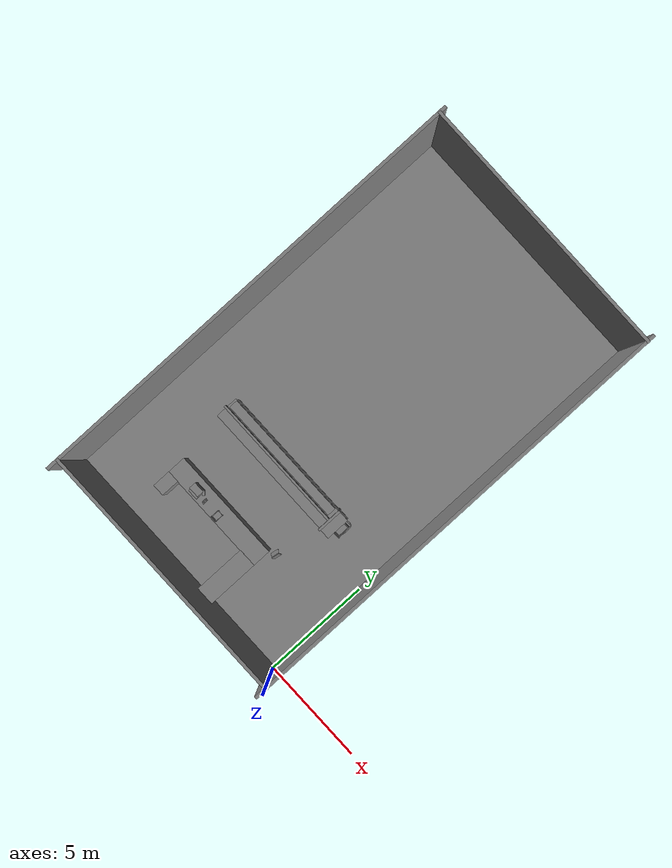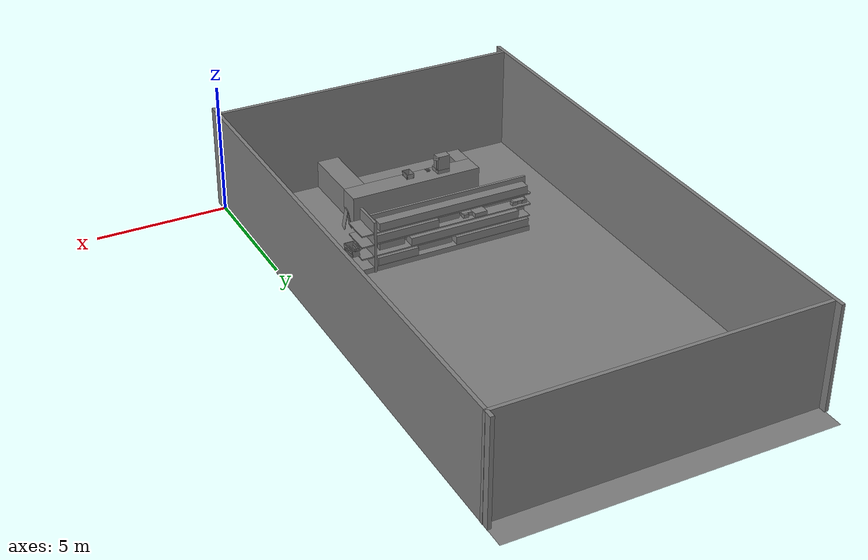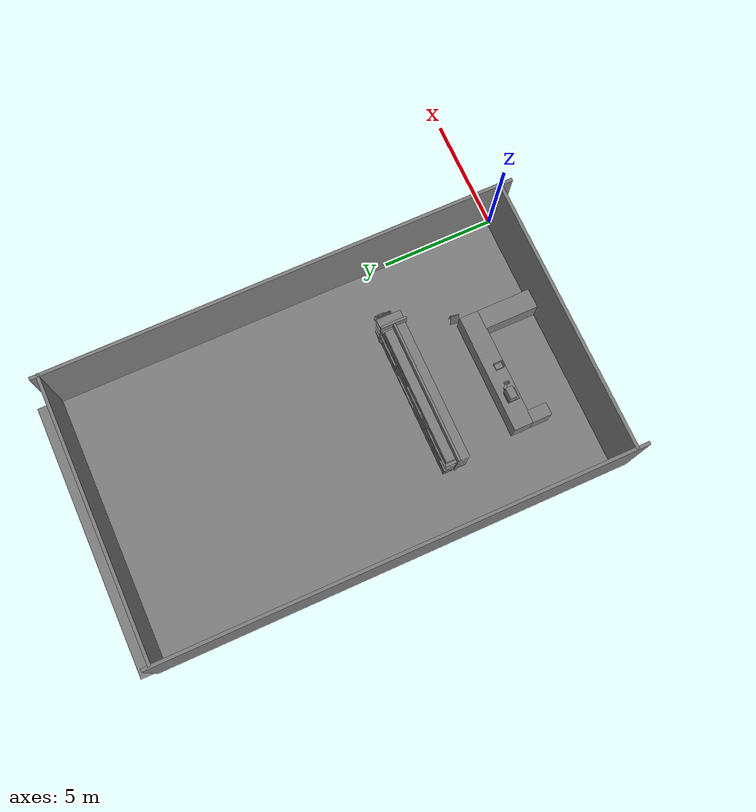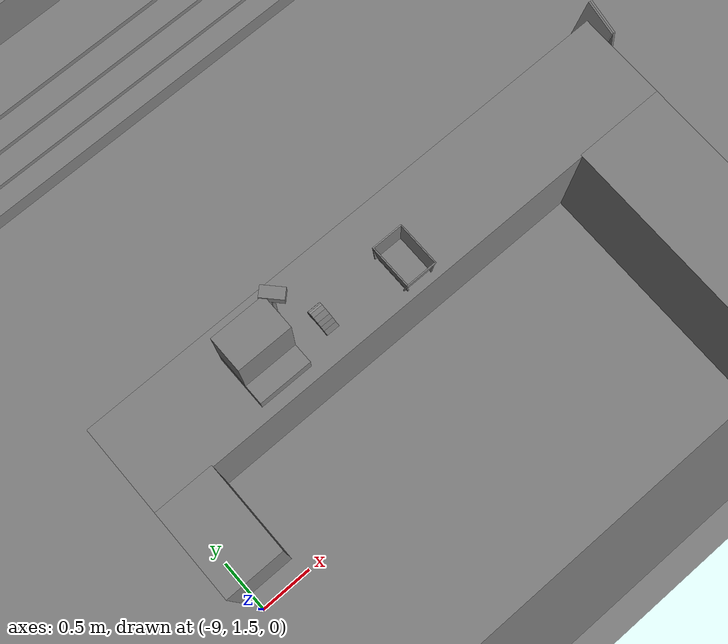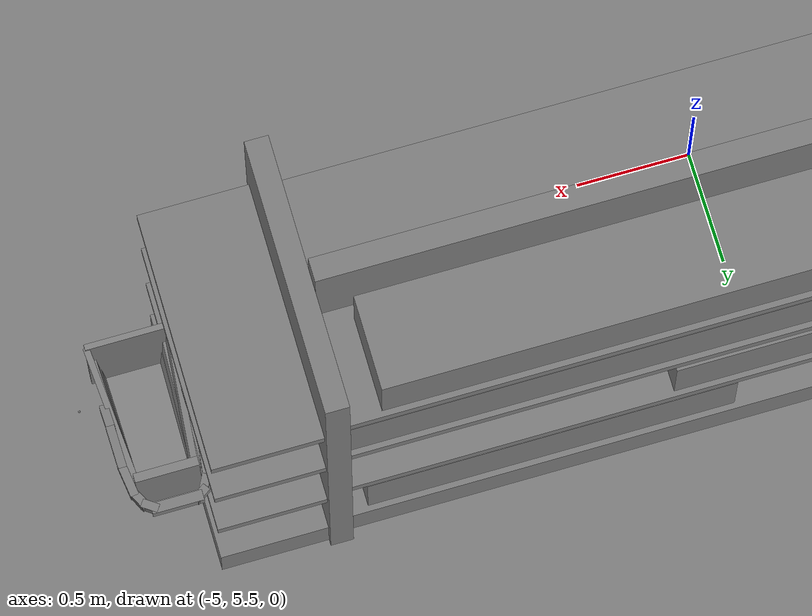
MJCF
<mujoco>
    <option gravity="0.000000000 0.000000000 -9.810000420" timestep="0.0166666" integrator="implicitfast" density="1.225" viscosity="1.8000001e-05" noslip_iterations="10" iterations="100" sdf_iterations="50">
        <flag multiccd="disable"/>
    </option>
    <size memory="1000M"/>
    <compiler coordinate="local"/>
    <worldbody>
        <light cutoff="30" pos="0 1 1" dir="0 -1 -2"/>
        <light cutoff="30" pos="0 -1 1" dir="0 1 -2"/>
        <body pos="-2.436573029 6.404376507 0.137849092" euler="0.000000000 0.000000000 0.000000000" name="[36900968218178]_shoppingtrolley_01">
            <geom contype="1" conaffinity="1" density="1000" type="box" material="" rgba="0.500000000 0.500000000 0.500000000 1.000000000" solimp="0.899999976 0.949999988 0.001000000" friction="1.000000000 0.005000000 0.000100000" solref="0.020000000 1.000000000" margin="0" condim="3" group="0" pos="0.148195267 -0.199506566 0.782808602" quat="0.998808920 0.017156634 0.026950166 0.036880098" size="0.013499999 0.305999994 0.063000001" name="[36900968218178]_geom_493A329C_5990_46A5_895D_4EA9801C6576"/>
            <geom contype="1" conaffinity="1" density="1000" type="box" material="" rgba="0.500000000 0.500000000 0.500000000 1.000000000" solimp="0.899999976 0.949999988 0.001000000" friction="1.000000000 0.005000000 0.000100000" solref="0.020000000 1.000000000" margin="0" condim="3" group="0" pos="-0.000005364 0.100332208 0.734785020" quat="0.999668717 0.025737956 -0.000000010 0.000000000" size="0.135000005 0.019800000 0.152999997" name="[36900968218178]_geom_7B9D5223_EA58_4FCF_A90B_422C47EDF05C"/>
            <geom contype="1" conaffinity="1" density="1000" type="box" material="" rgba="0.500000000 0.500000000 0.500000000 1.000000000" solimp="0.899999976 0.949999988 0.001000000" friction="1.000000000 0.005000000 0.000100000" solref="0.020000000 1.000000000" margin="0" condim="3" group="0" pos="-0.169898406 -0.043119621 0.915120542" quat="0.687021017 0.726584017 -0.005590606 -0.006832919" size="0.017999999 0.022499999 0.089999996" name="[36900968218178]_geom_B75A1290_9F6E_405B_9444_A0F54B7F70F9"/>
            <geom contype="1" conaffinity="1" density="1000" type="box" material="" rgba="0.500000000 0.500000000 0.500000000 1.000000000" solimp="0.899999976 0.949999988 0.001000000" friction="1.000000000 0.005000000 0.000100000" solref="0.020000000 1.000000000" margin="0" condim="3" group="0" pos="-0.169898406 -0.178061336 0.864131629" quat="0.916343808 -0.400392294 -0.000000045 0.000000030" size="0.017999999 0.022499999 0.089999996" name="[36900968218178]_geom_55966F62_25B7_4161_86FD_2AC70AA9FB9F"/>
            <geom contype="1" conaffinity="1" density="1000" type="box" material="" rgba="0.500000000 0.500000000 0.500000000 1.000000000" solimp="0.899999976 0.949999988 0.001000000" friction="1.000000000 0.005000000 0.000100000" solref="0.020000000 1.000000000" margin="0" condim="3" group="0" pos="0.103667587 0.233050480 0.912927270" quat="0.634205043 -0.622199059 -0.324503720 0.324576139" size="0.017999999 0.022499999 0.035999998" name="[36900968218178]_geom_39522934_3800_41D7_8B63_53F15BE7BF81"/>
            <geom contype="1" conaffinity="1" density="1000" type="box" material="" rgba="0.500000000 0.500000000 0.500000000 1.000000000" solimp="0.899999976 0.949999988 0.001000000" friction="1.000000000 0.005000000 0.000100000" solref="0.020000000 1.000000000" margin="0" condim="3" group="0" pos="0.169898629 -0.178061336 0.864131629" quat="0.916343808 -0.400392294 -0.000000045 0.000000030" size="0.017999999 0.022499999 0.089999996" name="[36900968218178]_geom_866BB7F4_9251_4CC0_A5FA_F5151B6FEFB7"/>
            <geom contype="1" conaffinity="1" density="1000" type="box" material="" rgba="0.500000000 0.500000000 0.500000000 1.000000000" solimp="0.899999976 0.949999988 0.001000000" friction="1.000000000 0.005000000 0.000100000" solref="0.020000000 1.000000000" margin="0" condim="3" group="0" pos="0.169898629 -0.043119621 0.915120542" quat="0.687029123 -0.726576388 -0.006509603 0.005963952" size="0.017999999 0.022499999 0.089999996" name="[36900968218178]_geom_AB932E67_B153_4682_82FD_D8B4B4F15FD1"/>
            <geom contype="1" conaffinity="1" density="1000" type="box" material="" rgba="0.500000000 0.500000000 0.500000000 1.000000000" solimp="0.899999976 0.949999988 0.001000000" friction="1.000000000 0.005000000 0.000100000" solref="0.020000000 1.000000000" margin="0" condim="3" group="0" pos="-0.005004787 0.248085022 0.912686050" quat="1.000000000 0.000000000 0.000000000 0.000000000" size="0.107999995 0.022499999 0.022499999" name="[36900968218178]_geom_BBA5AB77_4697_4EC2_8A17_60FD7227FB87"/>
            <geom contype="1" conaffinity="1" density="1000" type="box" material="" rgba="0.500000000 0.500000000 0.500000000 1.000000000" solimp="0.899999976 0.949999988 0.001000000" friction="1.000000000 0.005000000 0.000100000" solref="0.020000000 1.000000000" margin="0" condim="3" group="0" pos="-0.000004721 -0.174527690 0.560063601" quat="0.996704638 0.081116498 -0.000000004 0.000000000" size="0.126000002 0.287999988 0.009000000" name="[36900968218178]_geom_BF52CC2C_F786_4D62_96BF_E951FBCC6377"/>
            <geom contype="1" conaffinity="1" density="1000" type="box" material="" rgba="0.500000000 0.500000000 0.500000000 1.000000000" solimp="0.899999976 0.949999988 0.001000000" friction="1.000000000 0.005000000 0.000100000" solref="0.020000000 1.000000000" margin="0" condim="3" group="0" pos="0.134013891 0.200098798 0.912192523" quat="0.692574680 -0.680924535 -0.166899428 0.169783980" size="0.017999999 0.022499999 0.035999998" name="[36900968218178]_geom_BFBB4013_E9FC_42F4_B1B6_622476A4509F"/>
            <geom contype="1" conaffinity="1" density="1000" type="box" material="" rgba="0.500000000 0.500000000 0.500000000 1.000000000" solimp="0.899999976 0.949999988 0.001000000" friction="1.000000000 0.005000000 0.000100000" solref="0.020000000 1.000000000" margin="0" condim="3" group="0" pos="-0.135714188 -0.191051379 0.694841146" quat="0.997147322 0.056064609 -0.045779683 -0.021407485" size="0.013499999 0.287999988 0.053999998" name="[36900968218178]_geom_27A80C05_354F_4542_92DA_B3536C2B7776"/>
            <geom contype="1" conaffinity="1" density="1000" type="box" material="" rgba="0.500000000 0.500000000 0.500000000 1.000000000" solimp="0.899999976 0.949999988 0.001000000" friction="1.000000000 0.005000000 0.000100000" solref="0.020000000 1.000000000" margin="0" condim="3" group="0" pos="0.141839072 -0.191051379 0.702451229" quat="0.997147262 0.056065105 0.045779929 0.021407485" size="0.013499999 0.287999988 0.053999998" name="[36900968218178]_geom_B4A858F5_BA6F_4904_8FDE_0DB855E446EF"/>
            <geom contype="1" conaffinity="1" density="1000" type="box" material="" rgba="0.500000000 0.500000000 0.500000000 1.000000000" solimp="0.899999976 0.949999988 0.001000000" friction="1.000000000 0.005000000 0.000100000" solref="0.020000000 1.000000000" margin="0" condim="3" group="0" pos="-0.142927840 -0.199506134 0.784674108" quat="0.998421252 0.016904408 -0.027109101 -0.046199299" size="0.013499999 0.305999994 0.063000001" name="[36900968218178]_geom_00488905_0616_4D35_90CD_EC21B41588DC"/>
            <geom contype="1" conaffinity="1" density="1000" type="box" material="" rgba="0.500000000 0.500000000 0.500000000 1.000000000" solimp="0.899999976 0.949999988 0.001000000" friction="1.000000000 0.005000000 0.000100000" solref="0.020000000 1.000000000" margin="0" condim="3" group="0" pos="-0.000006008 -0.484932661 0.670727849" quat="0.997585475 0.069449045 -0.000000004 -0.000000089" size="0.179999992 0.013499999 0.170999989" name="[36900968218178]_geom_4EB6225C_22C1_4288_800E_0EEC62479A5C"/>
            <geom contype="1" conaffinity="1" density="1000" type="box" material="" rgba="0.500000000 0.500000000 0.500000000 1.000000000" solimp="0.899999976 0.949999988 0.001000000" friction="1.000000000 0.005000000 0.000100000" solref="0.020000000 1.000000000" margin="0" condim="3" group="0" pos="-0.160832763 0.103427693 0.910528183" quat="0.711469591 0.699786782 -0.048386075 -0.042050660" size="0.017999999 0.022499999 0.071999997" name="[36900968218178]_geom_6F076AAF_D4F6_46C1_8515_A1B78E5C189C"/>
            <geom contype="1" conaffinity="1" density="1000" type="box" material="" rgba="0.500000000 0.500000000 0.500000000 1.000000000" solimp="0.899999976 0.949999988 0.001000000" friction="1.000000000 0.005000000 0.000100000" solref="0.020000000 1.000000000" margin="0" condim="3" group="0" pos="0.131482959 -0.182533979 0.598989725" quat="0.996607125 0.055331629 0.059003670 0.015205893" size="0.013499999 0.287999988 0.053999998" name="[36900968218178]_geom_36B85154_905D_44C1_A542_171AD24CE661"/>
            <geom contype="1" conaffinity="1" density="1000" type="box" material="" rgba="0.500000000 0.500000000 0.500000000 1.000000000" solimp="0.899999976 0.949999988 0.001000000" friction="1.000000000 0.005000000 0.000100000" solref="0.020000000 1.000000000" margin="0" condim="3" group="0" pos="-0.134013891 0.200098798 0.912192523" quat="0.694057047 0.679413557 -0.172947660 -0.163618833" size="0.017999999 0.022499999 0.035999998" name="[36900968218178]_geom_D4CAAEDC_902B_4AE0_8298_CD14540908FD"/>
            <geom contype="1" conaffinity="1" density="1000" type="box" material="" rgba="0.500000000 0.500000000 0.500000000 1.000000000" solimp="0.899999976 0.949999988 0.001000000" friction="1.000000000 0.005000000 0.000100000" solref="0.020000000 1.000000000" margin="0" condim="3" group="0" pos="-0.126757339 -0.182533979 0.598989725" quat="0.996607184 0.055331606 -0.059003651 -0.015205891" size="0.013499999 0.287999988 0.053999998" name="[36900968218178]_geom_AC0EFF9B_B431_4784_8D41_55EAD19F702B"/>
            <geom contype="1" conaffinity="1" density="1000" type="box" material="" rgba="0.500000000 0.500000000 0.500000000 1.000000000" solimp="0.899999976 0.949999988 0.001000000" friction="1.000000000 0.005000000 0.000100000" solref="0.020000000 1.000000000" margin="0" condim="3" group="0" pos="-0.107458733 0.238907143 0.911498845" quat="0.634576976 0.622505128 -0.330067992 -0.317575932" size="0.017999999 0.022499999 0.035999998" name="[36900968218178]_geom_78751682_7633_4E43_8CFC_20B2224BF5B8"/>
            <geom contype="1" conaffinity="1" density="1000" type="box" material="" rgba="0.500000000 0.500000000 0.500000000 1.000000000" solimp="0.899999976 0.949999988 0.001000000" friction="1.000000000 0.005000000 0.000100000" solref="0.020000000 1.000000000" margin="0" condim="3" group="0" pos="0.160832971 0.103427693 0.910528183" quat="0.711112797 -0.700149298 -0.042821646 0.047705106" size="0.017999999 0.022499999 0.071999997" name="[36900968218178]_geom_07E9D788_F89B_4452_A469_81ACEF3DD62F"/>
            <site size="0.005000000 0.005000000 0.005000000" rgba="0.500000000 0.500000000 0.500000000 1.000000000" pos="0.000000000 0.000000000 0.000000000" quat="1.000000000 0.000000000 0.000000000 0.000000000" group="0" type="sphere" name="[36900968218178]_shoppingtrolley_01"/>
        </body>
        <body pos="-7.168000221 2.823999882 1.227496982" euler="-0.283413887 0.056829713 -0.133293241" name="openloong_gripper_2f85_fix_base_usda_Pos">
            <geom contype="1" conaffinity="1" density="1000" type="box" material="" rgba="0.500000000 0.500000000 0.500000000 1.000000000" solimp="0.899999976 0.949999988 0.001000000" friction="1.000000000 0.005000000 0.000100000" solref="0.020000000 1.000000000" margin="0" condim="3" group="0" pos="-0.002278805 0.074524641 -0.004134178" quat="0.315989256 0.948762834 0.000000000 0.000000000" size="0.059999999 0.013000000 0.035000000" name="openloong_gripper_2f85_fix_base_usda_geom_0DAB15F4_48B0_4D90_9C60_6542030CD53F"/>
            <geom contype="1" conaffinity="1" density="1000" type="box" material="" rgba="0.500000000 0.500000000 0.500000000 1.000000000" solimp="0.899999976 0.949999988 0.001000000" friction="1.000000000 0.005000000 0.000100000" solref="0.020000000 1.000000000" margin="0" condim="3" group="0" pos="-0.002278805 0.078031301 0.008128285" quat="0.990447283 -0.137893349 -0.000000000 0.000000000" size="0.059999999 0.010000000 0.035000000" name="openloong_gripper_2f85_fix_base_usda_geom_E2A2C2B3_3DEA_41FA_A2DB_9870155AAA8C"/>
            <geom contype="1" conaffinity="1" density="1000" type="box" material="" rgba="0.500000000 0.500000000 0.500000000 1.000000000" solimp="0.899999976 0.949999988 0.001000000" friction="1.000000000 0.005000000 0.000100000" solref="0.020000000 1.000000000" margin="0" condim="3" group="0" pos="-0.002278805 0.080785275 -0.002596974" quat="0.287325412 -0.957833171 0.000000000 -0.000000000" size="0.059999999 0.013000000 0.035000000" name="openloong_gripper_2f85_fix_base_usda_geom_47D7D199_7209_4DE8_94AA_FC5DE6B532AA"/>
            <geom contype="1" conaffinity="1" density="1000" type="box" material="" rgba="0.500000000 0.500000000 0.500000000 1.000000000" solimp="0.899999976 0.949999988 0.001000000" friction="1.000000000 0.005000000 0.000100000" solref="0.020000000 1.000000000" margin="0" condim="3" group="0" pos="-0.002278805 -0.098804474 -0.020147085" quat="0.988851428 0.148906425 0.000000000 -0.000000000" size="0.059999999 0.022000000 0.020000000" name="openloong_gripper_2f85_fix_base_usda_geom_063C8224_1F60_4912_8E01_D19DFBBA48DE"/>
            <geom contype="1" conaffinity="1" density="1000" type="box" material="" rgba="0.500000000 0.500000000 0.500000000 1.000000000" solimp="0.899999976 0.949999988 0.001000000" friction="1.000000000 0.005000000 0.000100000" solref="0.020000000 1.000000000" margin="0" condim="3" group="0" pos="-0.002279282 0.019920349 0.012102842" quat="0.995421529 0.095583312 -0.000000000 0.000000000" size="0.059999999 0.025000000 0.026000001" name="openloong_gripper_2f85_fix_base_usda_geom_1023F0BF_7C29_4B6B_9016_8BA7A8328070"/>
            <geom contype="1" conaffinity="1" density="1000" type="box" material="" rgba="0.500000000 0.500000000 0.500000000 1.000000000" solimp="0.899999976 0.949999988 0.001000000" friction="1.000000000 0.005000000 0.000100000" solref="0.020000000 1.000000000" margin="0" condim="3" group="0" pos="-0.002279282 0.005734444 -0.014276981" quat="0.999571502 -0.029275293 -0.000000000 0.000000000" size="0.059999999 0.050000001 0.010000000" name="openloong_gripper_2f85_fix_base_usda_geom_A0698009_1238_4864_A4EB_D2620DE7FE06"/>
            <geom contype="1" conaffinity="1" density="1000" type="box" material="" rgba="0.500000000 0.500000000 0.500000000 1.000000000" solimp="0.899999976 0.949999988 0.001000000" friction="1.000000000 0.005000000 0.000100000" solref="0.020000000 1.000000000" margin="0" condim="3" group="0" pos="-0.002278805 0.079460382 0.007771969" quat="0.922590315 -0.385781497 -0.000000000 0.000000000" size="0.059999999 0.010000000 0.035000000" name="openloong_gripper_2f85_fix_base_usda_geom_BB1FB435_B826_439B_80F2_00647924A1B3"/>
            <geom contype="1" conaffinity="1" density="1000" type="box" material="" rgba="0.500000000 0.500000000 0.500000000 1.000000000" solimp="0.899999976 0.949999988 0.001000000" friction="1.000000000 0.005000000 0.000100000" solref="0.020000000 1.000000000" margin="0" condim="3" group="0" pos="-0.002279282 0.081384182 -0.001320124" quat="0.590483606 -0.807049692 0.000000000 0.000000000" size="0.059999999 0.013000000 0.035000000" name="openloong_gripper_2f85_fix_base_usda_geom_DF10EE9E_5A3D_4479_B4CD_7528A5C698AD"/>
            <geom contype="1" conaffinity="1" density="1000" type="box" material="" rgba="0.500000000 0.500000000 0.500000000 1.000000000" solimp="0.899999976 0.949999988 0.001000000" friction="1.000000000 0.005000000 0.000100000" solref="0.020000000 1.000000000" margin="0" condim="3" group="0" pos="-0.002278805 -0.059297562 -0.007972836" quat="0.988851428 0.148906425 0.000000000 -0.000000000" size="0.059999999 0.020000000 0.022000000" name="openloong_gripper_2f85_fix_base_usda_geom_F2680944_93C0_4C36_B18B_E263C7125DAB"/>
            <geom contype="1" conaffinity="1" density="1000" type="box" material="" rgba="0.500000000 0.500000000 0.500000000 1.000000000" solimp="0.899999976 0.949999988 0.001000000" friction="1.000000000 0.005000000 0.000100000" solref="0.020000000 1.000000000" margin="0" condim="3" group="0" pos="-0.002278805 0.076618671 -0.004656911" quat="0.004634960 0.999989390 -0.000000000 0.000000000" size="0.059999999 0.013000000 0.035000000" name="openloong_gripper_2f85_fix_base_usda_geom_787D594C_D7B0_4800_96A9_0931D82D3351"/>
            <geom contype="1" conaffinity="1" density="1000" type="box" material="" rgba="0.500000000 0.500000000 0.500000000 1.000000000" solimp="0.899999976 0.949999988 0.001000000" friction="1.000000000 0.005000000 0.000100000" solref="0.020000000 1.000000000" margin="0" condim="3" group="0" pos="-0.002279282 -0.021952629 0.002959967" quat="0.991270185 0.131847635 0.000000000 -0.000000000" size="0.059999999 0.020000000 0.024000000" name="openloong_gripper_2f85_fix_base_usda_geom_042A3478_5EAE_4DD7_9948_D37097F5C5F7"/>
            <geom contype="1" conaffinity="1" density="1000" type="box" material="" rgba="0.500000000 0.500000000 0.500000000 1.000000000" solimp="0.899999976 0.949999988 0.001000000" friction="1.000000000 0.005000000 0.000100000" solref="0.020000000 1.000000000" margin="0" condim="3" group="0" pos="-0.002278805 0.081418991 0.002587795" quat="0.803492188 -0.595315576 0.000000000 0.000000000" size="0.059999999 0.013000000 0.035000000" name="openloong_gripper_2f85_fix_base_usda_geom_3FDA1C5B_5B33_4474_91C3_673196D5C63F"/>
            <geom contype="1" conaffinity="1" density="1000" type="box" material="" rgba="0.500000000 0.500000000 0.500000000 1.000000000" solimp="0.899999976 0.949999988 0.001000000" friction="1.000000000 0.005000000 0.000100000" solref="0.020000000 1.000000000" margin="0" condim="3" group="0" pos="-0.002278805 0.061115503 0.008545756" quat="0.999325931 0.036714435 -0.000000000 -0.000000000" size="0.059999999 0.020000000 0.035000000" name="openloong_gripper_2f85_fix_base_usda_geom_90EA9C6F_497C_45BB_96E1_393CD6AAD0F0"/>
            <freejoint name="openloong_gripper_2f85_fix_base_usda_pos_scan"/>
        </body>
        <body pos="-6.332345009 2.779978037 1.034067392" euler="0.000000000 0.000000000 0.000000000" name="openloong_gripper_2f85_fix_base_usda_basket">
            <geom contype="1" conaffinity="1" density="100000" type="box" material="" rgba="0.500000000 0.500000000 0.500000000 1.000000000" solimp="0.899999976 0.949999988 0.001000000" friction="1.000000000 0.899999976 0.000100000" solref="0.020000000 1.000000000" margin="0" condim="3" group="0" pos="-0.172339439 0.000000000 0.168361664" quat="0.706172407 -0.036353018 -0.036353093 0.706170976" size="0.200000003 0.006000000 0.108000003" name="openloong_gripper_2f85_fix_base_usda_geom_68B148CA_6320_4CD0_B1A7_D307E6DFF378"/>
            <geom contype="1" conaffinity="1" density="100000" type="box" material="" rgba="0.500000000 0.500000000 0.500000000 1.000000000" solimp="0.899999976 0.949999988 0.001000000" friction="1.000000000 0.899999976 0.000100000" solref="0.020000000 1.000000000" margin="0" condim="3" group="0" pos="-0.039724827 -0.188568115 0.167089701" quat="0.997537494 0.070135131 0.000000000 0.000000000" size="0.150000006 0.006000000 0.108000003" name="openloong_gripper_2f85_fix_base_usda_geom_8C970C71_4BFC_4429_AC38_EB9014AF59A7"/>
            <geom contype="1" conaffinity="1" density="100000" type="box" material="" rgba="0.500000000 0.500000000 0.500000000 1.000000000" solimp="0.899999976 0.949999988 0.001000000" friction="1.000000000 0.899999976 0.000100000" solref="0.020000000 1.000000000" margin="0" condim="3" group="0" pos="-0.039724827 0.188377380 0.167089701" quat="0.997489929 -0.070808925 0.000000000 0.000000000" size="0.150000006 0.006000000 0.108000003" name="openloong_gripper_2f85_fix_base_usda_geom_2BA16091_30E5_48DE_A7D6_55C71D836012"/>
            <geom contype="1" conaffinity="1" density="100000" type="box" material="" rgba="0.500000000 0.500000000 0.500000000 1.000000000" solimp="0.899999976 0.949999988 0.001000000" friction="1.000000000 0.899999976 0.000100000" solref="0.020000000 1.000000000" margin="0" condim="3" group="0" pos="-0.039724827 0.000000000 0.068126202" quat="1.000000000 0.000000000 0.000000000 0.000000000" size="0.129999995 0.174999997 0.006000000" name="openloong_gripper_2f85_fix_base_usda_geom_60E38B7E_99B3_4D1A_84A2_F564F44E9B2C"/>
            <geom contype="1" conaffinity="1" density="100000" type="box" material="" rgba="0.500000000 0.500000000 0.500000000 1.000000000" solimp="0.899999976 0.949999988 0.001000000" friction="1.000000000 0.899999976 0.000100000" solref="0.020000000 1.000000000" margin="0" condim="3" group="0" pos="0.094372749 0.000000000 0.168361664" quat="0.706172049 0.036353335 0.036353379 0.706171215" size="0.200000003 0.006000000 0.108000003" name="openloong_gripper_2f85_fix_base_usda_geom_4856F56C_DFCE_49DE_8B59_3B5D7B84422B"/>
            <freejoint name="openloong_gripper_2f85_fix_base_usda_basket_joint"/>
            <site size="0.005000000 0.005000000 0.005000000" rgba="0.500000000 0.500000000 0.500000000 1.000000000" pos="0.000000000 0.000000000 0.000000000" quat="1.000000000 0.000000000 0.000000000 0.000000000" group="0" type="sphere" name="openloong_gripper_2f85_fix_base_usda_basketsite"/>
        </body>
        <body pos="-3.510578632 3.403555870 -0.000000100" euler="0.000000000 0.000000000 40.200675964" name="openloong_gripper_2f85_fix_base_usda_PZ">
            <geom contype="1" conaffinity="1" density="1000" type="box" material="" rgba="0.500000000 0.500000000 0.500000000 1.000000000" solimp="0.899999976 0.949999988 0.001000000" friction="1.000000000 0.005000000 0.000100000" solref="0.020000000 1.000000000" margin="0" condim="3" group="0" pos="-0.047453165 0.056484699 0.373715430" quat="0.934750080 0.077914521 0.028795123 0.345459938" size="0.180000007 0.010000000 0.379999995" name="openloong_gripper_2f85_fix_base_usda_geom_B62ED080_A22F_44A8_BFA8_895CD93DDCBF"/>
            <geom contype="1" conaffinity="1" density="1000" type="box" material="" rgba="0.500000000 0.500000000 0.500000000 1.000000000" solimp="0.899999976 0.949999988 0.001000000" friction="1.000000000 0.005000000 0.000100000" solref="0.020000000 1.000000000" margin="0" condim="3" group="0" pos="0.047452450 -0.054376602 0.374072611" quat="0.934387863 -0.082143910 -0.030358355 0.345326364" size="0.180000007 0.010000000 0.379999995" name="openloong_gripper_2f85_fix_base_usda_geom_215E42F8_EA5B_42E6_9C28_36FD50296FAF"/>
            <freejoint name="openloong_gripper_2f85_fix_base_usda_PZ"/>
        </body>
        <body pos="0.000000000 0.000000000 0.000000000" euler="0.000000000 0.000000000 0.000000000" name="Interactive Objects_Interactive Objects"/>
        <body pos="0.000000000 0.000000000 0.000000000" euler="0.000000000 0.000000000 0.000000000" name=" Static Objects_ Static Objects">
            <geom contype="1" conaffinity="1" density="1000" type="box" material="" rgba="0.500000000 0.500000000 0.500000000 1.000000000" solimp="0.899999976 0.949999988 0.001000000" friction="1.000000000 0.005000000 0.000100000" solref="0.020000000 1.000000000" margin="0" condim="3" group="0" pos="-3.101639986 6.150595188 1.018643856" quat="1.000000000 0.000000000 0.000000000 0.000000000" size="0.050000001 0.579999983 1.019999981" name=" Static Objects_geom_B79A1EDF_447B_4961_866E_312D65530F4F"/>
            <geom contype="1" conaffinity="1" density="1000" type="box" material="" rgba="0.500000000 0.500000000 0.500000000 1.000000000" solimp="0.899999976 0.949999988 0.001000000" friction="1.000000000 0.005000000 0.000100000" solref="0.020000000 1.000000000" margin="0" condim="3" group="0" pos="-2.825197220 6.153595448 1.115278244" quat="0.707107067 0.000000000 0.000000000 0.707106471" size="0.550000012 0.239999995 0.025000000" name=" Static Objects_geom_6206EB89_A990_4329_8A86_9B478AA6893D"/>
            <geom contype="1" conaffinity="1" density="1000" type="box" material="" rgba="0.500000000 0.500000000 0.500000000 1.000000000" solimp="0.899999976 0.949999988 0.001000000" friction="1.000000000 0.005000000 0.000100000" solref="0.020000000 1.000000000" margin="0" condim="3" group="0" pos="-2.825197220 6.153595448 0.097434282" quat="0.707107067 0.000000000 0.000000000 0.707106471" size="0.550000012 0.239999995 0.098999999" name=" Static Objects_geom_A5DBEE61_1A24_4AEC_8F83_51CCB897F8AE"/>
            <geom contype="1" conaffinity="1" density="1000" type="box" material="" rgba="0.500000000 0.500000000 0.500000000 1.000000000" solimp="0.899999976 0.949999988 0.001000000" friction="1.000000000 0.005000000 0.000100000" solref="0.020000000 1.000000000" margin="0" condim="3" group="0" pos="-6.293097973 6.153595448 1.114443064" quat="0.707107067 0.000000000 0.000000000 0.707106471" size="0.529999971 3.134999990 0.025000000" name=" Static Objects_geom_D1648520_969A_4CDD_BEE6_EB0B8347C0AC"/>
            <geom contype="1" conaffinity="1" density="1000" type="box" material="" rgba="0.500000000 0.500000000 0.500000000 1.000000000" solimp="0.899999976 0.949999988 0.001000000" friction="1.000000000 0.005000000 0.000100000" solref="0.020000000 1.000000000" margin="0" condim="3" group="0" pos="-2.825197220 6.153595448 1.563861728" quat="0.707107067 0.000000000 0.000000000 0.707106471" size="0.550000012 0.239999995 0.025000000" name=" Static Objects_geom_408A718A_8652_4289_99B1_6A9F47F961FB"/>
            <geom contype="1" conaffinity="1" density="1000" type="box" material="" rgba="0.500000000 0.500000000 0.500000000 1.000000000" solimp="0.899999976 0.949999988 0.001000000" friction="1.000000000 0.005000000 0.000100000" solref="0.020000000 1.000000000" margin="0" condim="3" group="0" pos="-6.311686516 6.153595448 1.018643856" quat="0.707107067 0.000000000 0.000000000 0.707106471" size="0.050000001 3.150000095 1.019999981" name=" Static Objects_geom_D35B8E24_A76A_4D80_B6E5_C45B1E6F470D"/>
            <geom contype="1" conaffinity="1" density="1000" type="box" material="" rgba="0.500000000 0.500000000 0.500000000 1.000000000" solimp="0.899999976 0.949999988 0.001000000" friction="1.000000000 0.005000000 0.000100000" solref="0.020000000 1.000000000" margin="0" condim="3" group="0" pos="-6.286010742 6.153595448 0.096129179" quat="0.707107067 0.000000000 0.000000000 0.707106471" size="0.529999971 3.134999990 0.098999999" name=" Static Objects_geom_362249B5_C90E_4B8C_A5E7_4FBC4D2DD3DD"/>
            <geom contype="1" conaffinity="1" density="1000" type="box" material="" rgba="0.500000000 0.500000000 0.500000000 1.000000000" solimp="0.899999976 0.949999988 0.001000000" friction="1.000000000 0.005000000 0.000100000" solref="0.020000000 1.000000000" margin="0" condim="3" group="0" pos="-2.825197220 6.153595448 0.629031777" quat="0.707107067 0.000000000 0.000000000 0.707106471" size="0.550000012 0.239999995 0.025000000" name=" Static Objects_geom_3467EC53_9FB0_43C5_A846_DF98F2F89DA1"/>
            <geom contype="1" conaffinity="1" density="1000" type="box" material="" rgba="0.500000000 0.500000000 0.500000000 1.000000000" solimp="0.899999976 0.949999988 0.001000000" friction="1.000000000 0.005000000 0.000100000" solref="0.020000000 1.000000000" margin="0" condim="3" group="0" pos="-6.286010742 6.153595448 1.563861728" quat="0.707107067 0.000000000 0.000000000 0.707106471" size="0.529999971 3.134999990 0.025000000" name=" Static Objects_geom_55F06909_1314_40CB_9DE5_D19EDA0BBEF8"/>
            <geom contype="1" conaffinity="1" density="1000" type="box" material="" rgba="0.500000000 0.500000000 0.500000000 1.000000000" solimp="0.899999976 0.949999988 0.001000000" friction="1.000000000 0.005000000 0.000100000" solref="0.020000000 1.000000000" margin="0" condim="3" group="0" pos="-6.286010742 6.153595448 0.629031777" quat="0.707107067 0.000000000 0.000000000 0.707106471" size="0.529999971 3.134999990 0.025000000" name=" Static Objects_geom_9D8B450B_7F39_4827_B40C_324598094720"/>
            <geom contype="1" conaffinity="1" density="1000" type="box" material="" rgba="0.500000000 0.500000000 0.500000000 1.000000000" solimp="0.899999976 0.949999988 0.001000000" friction="1.000000000 0.005000000 0.000100000" solref="0.020000000 1.000000000" margin="0" condim="3" group="0" pos="-7.719123363 2.867671013 1.173410416" quat="1.000000000 0.000000000 0.000000000 0.000000000" size="0.250000000 0.250000000 0.079999998" name=" Static Objects_geom_D05869A1_5FB1_4B77_9BC7_BE51234CC8A1"/>
            <geom contype="1" conaffinity="1" density="1000" type="box" material="" rgba="0.500000000 0.500000000 0.500000000 1.000000000" solimp="0.899999976 0.949999988 0.001000000" friction="1.000000000 0.005000000 0.000100000" solref="0.020000000 1.000000000" margin="0" condim="3" group="0" pos="-7.408766270 3.088089943 1.776644945" quat="0.928051054 0.000000000 0.000000000 0.372453064" size="0.050000001 0.100000001 0.050000001" name=" Static Objects_geom_09DD9079_B8BF_491E_920C_85B2B0FD317C"/>
            <geom contype="1" conaffinity="1" density="1000" type="box" material="" rgba="0.500000000 0.500000000 0.500000000 1.000000000" solimp="0.899999976 0.949999988 0.001000000" friction="1.000000000 0.005000000 0.000100000" solref="0.020000000 1.000000000" margin="0" condim="3" group="0" pos="-7.719123363 2.958004713 1.530241251" quat="1.000000000 0.000000000 0.000000000 0.000000000" size="0.250000000 0.159999996 0.280000001" name=" Static Objects_geom_A2F46127_A62C_491A_B3C6_5BC2E2DE2F72"/>
            <geom contype="1" conaffinity="1" density="1000" type="cylinder" material="" rgba="0.500000000 0.500000000 0.500000000 1.000000000" solimp="0.899999976 0.949999988 0.001000000" friction="1.000000000 0.005000000 0.000100000" solref="0.020000000 1.000000000" margin="0" condim="3" group="0" pos="-7.427312374 3.069516420 1.502544641" quat="0.928051054 0.000000000 0.000000000 0.372453064" size="0.015000000 0.230000004 0.100000001" name=" Static Objects_geom_C71D0786_5890_4B5E_BD9E_A5E7AC9B53B6"/>
            <geom contype="1" conaffinity="1" density="1000" type="box" material="" rgba="0.500000000 0.500000000 0.500000000 1.000000000" solimp="0.899999976 0.949999988 0.001000000" friction="1.000000000 0.005000000 0.000100000" solref="0.020000000 1.000000000" margin="0" condim="3" group="0" pos="-7.437745571 3.067511320 1.289965630" quat="1.000000000 0.000000000 0.000000000 0.000000000" size="0.029999999 0.020000000 0.020000000" name=" Static Objects_geom_FD3D6CCC_2F4B_45C8_8C8C_F8AC6C0B5B3A"/>
            <geom contype="1" conaffinity="1" density="1000" type="box" material="" rgba="0.500000000 0.500000000 0.500000000 1.000000000" solimp="0.899999976 0.949999988 0.001000000" friction="1.000000000 0.005000000 0.000100000" solref="0.020000000 1.000000000" margin="0" condim="3" group="0" pos="-9.058088303 6.434794426 1.209077358" quat="1.000000000 0.000000000 0.000000000 0.000000000" size="0.250000000 0.100000001 0.070000000" name=" Static Objects_geom_62DF213F_7766_4A0F_A912_30774C77E3D2"/>
            <geom contype="1" conaffinity="1" density="1000" type="box" material="" rgba="0.500000000 0.500000000 0.500000000 1.000000000" solimp="0.899999976 0.949999988 0.001000000" friction="1.000000000 0.005000000 0.000100000" solref="0.020000000 1.000000000" margin="0" condim="3" group="0" pos="-7.886891365 6.459744930 0.352518857" quat="1.000000000 0.000000000 0.000000000 0.000000000" size="1.500000000 0.200000003 0.150000006" name=" Static Objects_geom_55286C9C_0EEA_45EB_BBFF_8A50737CB44F"/>
            <geom contype="1" conaffinity="1" density="1000" type="box" material="" rgba="0.500000000 0.500000000 0.500000000 1.000000000" solimp="0.899999976 0.949999988 0.001000000" friction="1.000000000 0.005000000 0.000100000" solref="0.020000000 1.000000000" margin="0" condim="3" group="0" pos="-9.237723351 6.464855671 1.209077358" quat="1.000000000 0.000000000 0.000000000 0.000000000" size="0.100000001 0.100000001 0.070000000" name=" Static Objects_geom_C82BBF85_0F95_4E37_8797_D64587853D74"/>
            <geom contype="1" conaffinity="1" density="1000" type="box" material="" rgba="0.500000000 0.500000000 0.500000000 1.000000000" solimp="0.899999976 0.949999988 0.001000000" friction="1.000000000 0.005000000 0.000100000" solref="0.020000000 1.000000000" margin="0" condim="3" group="0" pos="-6.924745083 6.362090111 1.214329123" quat="1.000000000 0.000000000 0.000000000 0.000000000" size="0.200000003 0.100000001 0.075000003" name=" Static Objects_geom_11C9E7A5_65EF_4C58_BBB7_044A8CAF63C6"/>
            <geom contype="1" conaffinity="1" density="1000" type="box" material="" rgba="0.500000000 0.500000000 0.500000000 1.000000000" solimp="0.899999976 0.949999988 0.001000000" friction="1.000000000 0.005000000 0.000100000" solref="0.020000000 1.000000000" margin="0" condim="3" group="0" pos="-4.407354832 6.459744930 1.292199373" quat="1.000000000 0.000000000 0.000000000 0.000000000" size="1.240000010 0.200000003 0.150000006" name=" Static Objects_geom_FD0E1632_E269_464D_954B_0F8F9A2F6A2C"/>
            <geom contype="1" conaffinity="1" density="1000" type="box" material="" rgba="0.500000000 0.500000000 0.500000000 1.000000000" solimp="0.899999976 0.949999988 0.001000000" friction="1.000000000 0.005000000 0.000100000" solref="0.020000000 1.000000000" margin="0" condim="3" group="0" pos="-5.611940861 6.318420410 0.350975692" quat="1.000000000 0.000000000 0.000000000 0.000000000" size="0.699999988 0.100000001 0.150000006" name=" Static Objects_geom_322C5A3B_97AD_495A_95AC_7C656FF04919"/>
            <geom contype="1" conaffinity="1" density="1000" type="box" material="" rgba="0.500000000 0.500000000 0.500000000 1.000000000" solimp="0.899999976 0.949999988 0.001000000" friction="1.000000000 0.005000000 0.000100000" solref="0.020000000 1.000000000" margin="0" condim="3" group="0" pos="-6.300771236 6.459744930 1.744376063" quat="1.000000000 0.000000000 0.000000000 0.000000000" size="3.000000000 0.200000003 0.150000006" name=" Static Objects_geom_14ECC90B_0234_40C4_B550_13C0726B8F6F"/>
            <geom contype="1" conaffinity="1" density="1000" type="box" material="" rgba="0.500000000 0.500000000 0.500000000 1.000000000" solimp="0.899999976 0.949999988 0.001000000" friction="1.000000000 0.005000000 0.000100000" solref="0.020000000 1.000000000" margin="0" condim="3" group="0" pos="-8.844120979 6.464855671 1.209077358" quat="1.000000000 0.000000000 0.000000000 0.000000000" size="0.100000001 0.100000001 0.070000000" name=" Static Objects_geom_D67924CB_DDCE_4201_8C13_761C71D7DEBD"/>
            <geom contype="1" conaffinity="1" density="1000" type="box" material="" rgba="0.500000000 0.500000000 0.500000000 1.000000000" solimp="0.899999976 0.949999988 0.001000000" friction="1.000000000 0.005000000 0.000100000" solref="0.020000000 1.000000000" margin="0" condim="3" group="0" pos="-6.824534416 6.447464466 1.212718010" quat="1.000000000 0.000000000 0.000000000 0.000000000" size="0.100000001 0.100000001 0.075000003" name=" Static Objects_geom_418FDEF4_7D5D_47A3_899E_317FEF782C23"/>
            <geom contype="1" conaffinity="1" density="1000" type="box" material="" rgba="0.500000000 0.500000000 0.500000000 1.000000000" solimp="0.899999976 0.949999988 0.001000000" friction="1.000000000 0.005000000 0.000100000" solref="0.020000000 1.000000000" margin="0" condim="3" group="0" pos="-6.751636982 6.459744930 0.800981164" quat="1.000000000 0.000000000 0.000000000 0.000000000" size="2.200000048 0.200000003 0.150000006" name=" Static Objects_geom_A1D4E281_7635_4159_8046_C5AE65AE602B"/>
            <geom contype="1" conaffinity="1" density="1000" type="box" material="" rgba="0.500000000 0.500000000 0.500000000 1.000000000" solimp="0.899999976 0.949999988 0.001000000" friction="1.000000000 0.005000000 0.000100000" solref="0.020000000 1.000000000" margin="0" condim="3" group="0" pos="-6.098561764 6.327973843 1.292199373" quat="1.000000000 0.000000000 0.000000000 0.000000000" size="0.500000000 0.100000001 0.150000006" name=" Static Objects_geom_48D25170_11C8_4523_8F3A_69F2FB3E1C26"/>
            <geom contype="1" conaffinity="1" density="1000" type="box" material="" rgba="0.500000000 0.500000000 0.500000000 1.000000000" solimp="0.899999976 0.949999988 0.001000000" friction="1.000000000 0.005000000 0.000100000" solref="0.020000000 1.000000000" margin="0" condim="3" group="0" pos="-3.907610416 6.318625927 0.800981164" quat="1.000000000 0.000000000 0.000000000 0.000000000" size="0.500000000 0.100000001 0.150000006" name=" Static Objects_geom_99C1C8AA_1BF0_4C21_A658_88FC7F3385B8"/>
            <geom contype="1" conaffinity="1" density="1000" type="box" material="" rgba="0.500000000 0.500000000 0.500000000 1.000000000" solimp="0.899999976 0.949999988 0.001000000" friction="1.000000000 0.005000000 0.000100000" solref="0.020000000 1.000000000" margin="0" condim="3" group="0" pos="-7.373087406 6.458900928 1.214329123" quat="1.000000000 0.000000000 0.000000000 0.000000000" size="0.250000000 0.200000003 0.075000003" name=" Static Objects_geom_1A5F3C8F_9FB7_4DDE_B6EE_F59924A0E71B"/>
            <geom contype="1" conaffinity="1" density="1000" type="box" material="" rgba="0.500000000 0.500000000 0.500000000 1.000000000" solimp="0.899999976 0.949999988 0.001000000" friction="1.000000000 0.005000000 0.000100000" solref="0.020000000 1.000000000" margin="0" condim="3" group="0" pos="-4.035642624 6.459744930 0.352518857" quat="1.000000000 0.000000000 0.000000000 0.000000000" size="0.800000012 0.200000003 0.150000006" name=" Static Objects_geom_B39A854C_1518_492D_92DB_2F00459205F1"/>
            <geom contype="1" conaffinity="1" density="1000" type="box" material="" rgba="0.500000000 0.500000000 0.500000000 1.000000000" solimp="0.899999976 0.949999988 0.001000000" friction="1.000000000 0.005000000 0.000100000" solref="0.020000000 1.000000000" margin="0" condim="3" group="0" pos="-6.460197449 2.937205315 0.548931718" quat="1.000000000 0.000000000 0.000000000 0.000000000" size="2.650000095 0.430000007 0.550000012" name=" Static Objects_geom_28DFA09E_5E8E_4998_B56E_0990CEAC6910"/>
            <geom contype="1" conaffinity="1" density="1000" type="box" material="" rgba="0.500000000 0.500000000 0.500000000 1.000000000" solimp="0.899999976 0.949999988 0.001000000" friction="1.000000000 0.005000000 0.000100000" solref="0.020000000 1.000000000" margin="0" condim="3" group="0" pos="-4.240264893 1.327049494 0.549888909" quat="1.000000000 0.000000000 0.000000000 0.000000000" size="0.430000007 1.200000048 0.550000012" name=" Static Objects_geom_CA820E9D_1FC3_42A1_A221_437EE5ECDA49"/>
            <geom contype="1" conaffinity="1" density="1000" type="box" material="" rgba="0.500000000 0.500000000 0.500000000 1.000000000" solimp="0.899999976 0.949999988 0.001000000" friction="1.000000000 0.005000000 0.000100000" solref="0.020000000 1.000000000" margin="0" condim="3" group="0" pos="-8.830721855 2.096410990 0.549305558" quat="1.000000000 0.000000000 0.000000000 0.000000000" size="0.280000001 0.430000007 0.550000012" name=" Static Objects_geom_C0F744B0_CB6C_44F8_877F_FFA2A3410607"/>
            <geom contype="1" conaffinity="1" density="1000" type="plane" material="" rgba="0.500000000 0.500000000 0.500000000 1.000000000" solimp="0.899999976 0.949999988 0.001000000" friction="1.000000000 0.005000000 0.000100000" solref="0.020000000 1.000000000" margin="0" condim="3" group="0" pos="-6.000000000 10.399999619 0.000000000" quat="1.000000000 0.000000000 0.000000000 0.000000000" size="6.050000191 10.800000191 0.010000000" name=" Static Objects_geom_EE1A6E64_EFDE_4D21_920E_0F27DC3D7F04"/>
            <geom contype="1" conaffinity="1" density="1000" type="box" material="" rgba="0.500000000 0.500000000 0.500000000 1.000000000" solimp="0.899999976 0.949999988 0.001000000" friction="1.000000000 0.005000000 0.000100000" solref="0.020000000 1.000000000" margin="0" condim="3" group="0" pos="-6.000000000 0.035000000 2.000000000" quat="1.000000000 0.000000000 0.000000000 0.000000000" size="6.079999924 0.070000000 2.000000000" name=" Static Objects_geom_AC97D5A7_7AD2_4830_A314_DAA85485469B"/>
            <geom contype="1" conaffinity="1" density="1000" type="box" material="" rgba="0.500000000 0.500000000 0.500000000 1.000000000" solimp="0.899999976 0.949999988 0.001000000" friction="1.000000000 0.005000000 0.000100000" solref="0.020000000 1.000000000" margin="0" condim="3" group="0" pos="-6.000000000 20.159999847 2.000000000" quat="1.000000000 0.000000000 0.000000000 0.000000000" size="6.079999924 0.070000000 2.000000000" name=" Static Objects_geom_7B7D7ABE_3154_4958_9C82_9FD8747692AB"/>
            <geom contype="1" conaffinity="1" density="1000" type="box" material="" rgba="0.500000000 0.500000000 0.500000000 1.000000000" solimp="0.899999976 0.949999988 0.001000000" friction="1.000000000 0.005000000 0.000100000" solref="0.020000000 1.000000000" margin="0" condim="3" group="0" pos="0.000000000 10.000000000 2.000000000" quat="1.000000000 0.000000000 0.000000000 0.000000000" size="0.070000000 10.500000000 2.000000000" name=" Static Objects_geom_95E88AF4_018C_4D25_852C_CDE2A78352AC"/>
            <geom contype="1" conaffinity="1" density="1000" type="box" material="" rgba="0.500000000 0.500000000 0.500000000 1.000000000" solimp="0.899999976 0.949999988 0.001000000" friction="1.000000000 0.005000000 0.000100000" solref="0.020000000 1.000000000" margin="0" condim="3" group="0" pos="-12.050000191 10.000000000 2.000000000" quat="1.000000000 0.000000000 0.000000000 0.000000000" size="0.070000000 10.500000000 2.000000000" name=" Static Objects_geom_FC57A0E8_492E_4324_8CC1_39E9E4F54893"/>
        </body>
        <body pos="-2.162787437 6.180304527 -0.123990886" euler="0.000000000 0.000000000 180.000000000" mocap="true" name="openloong_gripper_2f85_fix_base_usda_leftHandMocap"/>
        <body pos="-2.162787437 6.180304527 -0.123990886" euler="0.000000000 0.000000000 180.000000000" mocap="true" name="openloong_gripper_2f85_fix_base_usda_rightHandMocap"/>
        <body pos="-2.162787437 6.180304527 1.076009154" euler="0.000000000 0.000000000 180.000000000" name="openloong_gripper_2f85_fix_base_usda_base_link">
            <geom contype="1" conaffinity="1" density="1000" type="mesh" material="" rgba="0.783999979 0.783999979 0.783999979 1.000000000" solimp="0.899999976 0.949999988 0.001000000" friction="1.000000000 0.005000000 0.000100000" solref="0.020000000 1.000000000" margin="0" condim="3" group="3" mesh="base_link" pos="0.000000000 0.000000000 0.000000000" quat="1.000000000 0.000000000 0.000000000 0.000000000" size="1.000000000 1.000000000 1.000000000" name="openloong_gripper_2f85_fix_base_usda__geom_7_B4781D8F_5F8C_4337_93BE_F3B1B239F0DC"/>
            <site size="0.005000000 0.005000000 0.005000000" rgba="0.500000000 0.500000000 0.500000000 1.000000000" pos="0.000000000 0.000000000 0.000000000" quat="1.000000000 0.000000000 0.000000000 0.000000000" group="0" type="sphere" name="openloong_gripper_2f85_fix_base_usda_imu"/>
            <inertial mass="22.447001" pos="-0.005664100 -0.001336700 0.238289997" diaginertia="0.374352545 0.277180195 0.220617250" quat="0.999247074 0.035235517 -0.015086859 0.006023135"/>
            <body pos="0.000000000 0.000000000 0.300000072" euler="0.000000000 0.000000000 0.000000000" name="openloong_gripper_2f85_fix_base_usda_dummy_body">
                <geom contype="1" conaffinity="1" density="1000" type="sphere" material="" rgba="0.783999979 0.783999979 0.783999979 1.000000000" solimp="0.899999976 0.949999988 0.001000000" friction="1.000000000 0.005000000 0.000100000" solref="0.020000000 1.000000000" margin="0" condim="3" group="3" pos="0.000000000 0.000000000 0.000000000" quat="1.000000000 0.000000000 0.000000000 0.000000000" size="0.010000000 0.000000000 0.000000000" name="openloong_gripper_2f85_fix_base_usda__geom_8_793277F9_F041_4767_8250_F5A94B3041F7"/>
                <joint armature="0.0099999998" stiffness="0" damping="0.1" axis="0.000000 0.000000 1.000000" type="hinge" name="openloong_gripper_2f85_fix_base_usda_dummy_joint"/>
                <site size="0.010000000 0.005000000 0.005000000" rgba="0.500000000 0.500000000 0.500000000 1.000000000" pos="0.000000000 0.000000000 0.000000000" quat="1.000000000 0.000000000 0.000000000 0.000000000" group="3" type="sphere" name="openloong_gripper_2f85_fix_base_usda_dummy_site"/>
            </body>
            <body pos="0.009000063 0.000000000 0.406399965" euler="0.000000000 0.000000000 0.000000000" name="openloong_gripper_2f85_fix_base_usda_Link_head_yaw">
                <geom contype="1" conaffinity="1" density="1000" type="mesh" material="" rgba="0.783999979 0.783999979 0.783999979 1.000000000" solimp="0.899999976 0.949999988 0.001000000" friction="1.000000000 0.005000000 0.000100000" solref="0.020000000 1.000000000" margin="0" condim="3" group="3" mesh="Link_head_yaw" pos="0.000000000 0.000000000 0.000000000" quat="1.000000000 0.000000000 0.000000000 0.000000000" size="1.000000000 1.000000000 1.000000000" name="openloong_gripper_2f85_fix_base_usda__geom_10_08C2771E_D933_4629_BE12_7C46C952CAE9"/>
                <inertial mass="0.84249002" pos="0.000000000 -0.002081400 0.044801001" diaginertia="0.000700588 0.000629000 0.000553812" quat="0.706933022 -0.015675601 0.015677100 0.706933022"/>
                <body pos="0.000000000 -0.034599781 0.048499942" euler="0.000000000 0.000000000 0.000000000" name="openloong_gripper_2f85_fix_base_usda_Link_head_pitch">
                    <geom contype="1" conaffinity="1" density="1000" type="mesh" material="" rgba="0.783999979 0.783999979 0.783999979 1.000000000" solimp="0.899999976 0.949999988 0.001000000" friction="1.000000000 0.005000000 0.000100000" solref="0.020000000 1.000000000" margin="0" condim="3" group="3" mesh="Link_head_pitch" pos="0.000000000 0.000000000 0.000000000" quat="1.000000000 0.000000000 0.000000000 0.000000000" size="1.000000000 1.000000000 1.000000000" name="openloong_gripper_2f85_fix_base_usda__geom_12_94C1B951_1147_4C0F_906A_B1F68A0EB668"/>
                    <inertial mass="1.3943" pos="0.020569000 0.033004001 0.125000000" diaginertia="0.006381400 0.006289940 0.004481460" quat="0.973390222 0.008406822 0.228157058 0.019624906"/>
                    <body pos="0.000000000 0.030000210 0.000000000" euler="0.000000000 0.000000000 0.000000000" name="openloong_gripper_2f85_fix_base_usda_neck_center_body">
                        <site size="0.010000000 0.005000000 0.005000000" rgba="0.500000000 0.500000000 0.500000000 1.000000000" pos="0.000000000 0.000000000 0.000000000" quat="1.000000000 0.000000000 0.000000000 0.000000000" group="3" type="sphere" name="openloong_gripper_2f85_fix_base_usda_neck_center_site"/>
                        <body pos="0.019999981 0.000000000 0.149999976" euler="-0.000002229 39.998176575 -90.000205994" name="openloong_gripper_2f85_fix_base_usda_camera_head">
                            <site size="0.010000000 0.005000000 0.005000000" rgba="0.500000000 0.500000000 0.500000000 1.000000000" pos="0.000000000 0.000000000 0.000000000" quat="1.000000000 0.000000000 0.000000000 0.000000000" group="3" type="sphere" name="openloong_gripper_2f85_fix_base_usda_camera_head_site"/>
                        </body>
                    </body>
                </body>
            </body>
            <body pos="0.003999949 -0.161600113 0.392199993" euler="0.000000000 0.000000000 0.000000000" name="openloong_gripper_2f85_fix_base_usda_Link_arm_r_01">
                <geom contype="1" conaffinity="1" density="1000" type="mesh" material="" rgba="0.783999979 0.783999979 0.783999979 1.000000000" solimp="0.899999976 0.949999988 0.001000000" friction="1.000000000 0.005000000 0.000100000" solref="0.020000000 1.000000000" margin="0" condim="3" group="3" mesh="Link_arm_r_01" pos="0.000000000 0.000000000 0.000000000" quat="1.000000000 0.000000000 0.000000000 0.000000000" size="1.000000000 1.000000000 1.000000000" name="openloong_gripper_2f85_fix_base_usda__geom_14_72191268_A56E_4F60_A644_5DBEBA625FE2"/>
                <joint armature="0.0099999998" stiffness="0" damping="1" axis="0.000000 -1.000000 0.000000" limited="true" range="-170.000015259 170.000015259" type="hinge" name="openloong_gripper_2f85_fix_base_usda_J_arm_r_01"/>
                <inertial mass="0.75641" pos="0.004494600 -0.038293999 -0.000001874" diaginertia="0.000842990 0.000803050 0.000587120" quat="-0.000163502 0.707098067 0.000812463 0.707115054"/>
                <body pos="-0.042000055 -0.040999889 0.000000000" euler="0.000000000 0.000000000 0.000000000" name="openloong_gripper_2f85_fix_base_usda_Link_arm_r_02">
                    <geom contype="1" conaffinity="1" density="1000" type="mesh" material="" rgba="0.783999979 0.783999979 0.783999979 1.000000000" solimp="0.899999976 0.949999988 0.001000000" friction="1.000000000 0.005000000 0.000100000" solref="0.020000000 1.000000000" margin="0" condim="3" group="3" mesh="Link_arm_r_02" pos="0.000000000 0.000000000 0.000000000" quat="1.000000000 0.000000000 0.000000000 0.000000000" size="1.000000000 1.000000000 1.000000000" name="openloong_gripper_2f85_fix_base_usda__geom_16_CD164694_3E0D_43F5_AE52_4943C1514655"/>
                    <joint armature="0.0099999998" stiffness="0" damping="1" axis="-1.000000 0.000000 0.000000" limited="true" range="-105.000244141 105.000244141" type="hinge" name="openloong_gripper_2f85_fix_base_usda_J_arm_r_02"/>
                    <inertial mass="0.98500001" pos="0.041999999 -0.067430697 0.000000000" diaginertia="0.002262690 0.001730990 0.001154020" quat="0.500000000 0.500000000 -0.500000000 0.500000000"/>
                    <body pos="0.042000055 -0.122600079 0.000000000" euler="0.000000000 0.000000000 0.000000000" name="openloong_gripper_2f85_fix_base_usda_Link_arm_r_03">
                        <geom contype="1" conaffinity="1" density="1000" type="mesh" material="" rgba="0.783999979 0.783999979 0.783999979 1.000000000" solimp="0.899999976 0.949999988 0.001000000" friction="1.000000000 0.005000000 0.000100000" solref="0.020000000 1.000000000" margin="0" condim="3" group="3" mesh="Link_arm_r_03" pos="0.000000000 0.000000000 0.000000000" quat="1.000000000 0.000000000 0.000000000 0.000000000" size="1.000000000 1.000000000 1.000000000" name="openloong_gripper_2f85_fix_base_usda__geom_18_5C45DE22_36FB_4C9C_B7B1_9687484AD4BD"/>
                        <joint armature="0.0099999998" stiffness="0" damping="1" axis="0.000000 -1.000000 0.000000" limited="true" range="-170.000015259 170.000015259" type="hinge" name="openloong_gripper_2f85_fix_base_usda_J_arm_r_03"/>
                        <inertial mass="0.95899999" pos="-0.001413580 -0.164663002 0.020757901" diaginertia="0.002101340 0.002064590 0.000754802" quat="0.560480952 0.454391927 -0.443732947 0.531497955"/>
                        <body pos="0.035300016 -0.177400112 0.024000049" euler="0.000000000 0.000000000 0.000000000" name="openloong_gripper_2f85_fix_base_usda_Link_arm_r_04">
                            <geom contype="1" conaffinity="1" density="1000" type="mesh" material="" rgba="0.783999979 0.783999979 0.783999979 1.000000000" solimp="0.899999976 0.949999988 0.001000000" friction="1.000000000 0.005000000 0.000100000" solref="0.020000000 1.000000000" margin="0" condim="3" group="3" mesh="Link_arm_r_04" pos="0.000000000 0.000000000 0.000000000" quat="1.000000000 0.000000000 0.000000000 0.000000000" size="1.000000000 1.000000000 1.000000000" name="openloong_gripper_2f85_fix_base_usda__geom_20_CD284B8A_433A_4875_A64E_CA628353F68B"/>
                            <joint armature="0.0099999998" stiffness="0" damping="1" axis="-1.000000 0.000000 0.000000" limited="true" range="0.000000000 170.000015259" type="hinge" name="openloong_gripper_2f85_fix_base_usda_J_arm_r_04"/>
                            <inertial mass="0.60000002" pos="-0.038727000 -0.060766999 -0.021003000" diaginertia="0.001092610 0.000712422 0.000645102" quat="0.327701002 0.632602990 -0.467366993 0.523443997"/>
                            <body pos="-0.035300016 -0.103499889 -0.024000049" euler="0.000000000 0.000000000 0.000000000" name="openloong_gripper_2f85_fix_base_usda_Link_arm_r_05">
                                <geom contype="1" conaffinity="1" density="1000" type="mesh" material="" rgba="0.783999979 0.783999979 0.783999979 1.000000000" solimp="0.899999976 0.949999988 0.001000000" friction="1.000000000 0.005000000 0.000100000" solref="0.020000000 1.000000000" margin="0" condim="3" group="3" mesh="Link_arm_r_05" pos="0.000000000 0.000000000 0.000000000" quat="1.000000000 0.000000000 0.000000000 0.000000000" size="1.000000000 1.000000000 1.000000000" name="openloong_gripper_2f85_fix_base_usda__geom_22_2A1EAA6A_9D54_415C_B473_FCE46DBE9544"/>
                                <joint armature="0.0099999998" stiffness="0" damping="1" axis="0.000000 -1.000000 0.000000" limited="true" range="-170.000015259 170.000015259" type="hinge" name="openloong_gripper_2f85_fix_base_usda_J_arm_r_05"/>
                                <inertial mass="0.68976003" pos="0.000032712 -0.068658002 -0.000111780" diaginertia="0.002522510 0.002411100 0.000448695" quat="0.707660973 0.706543028 -0.002603360 0.002470550"/>
                                <body pos="-0.026499987 -0.196499825 0.000000000" euler="0.000000000 0.000000000 0.000000000" name="openloong_gripper_2f85_fix_base_usda_Link_arm_r_06">
                                    <geom contype="1" conaffinity="1" density="1000" type="mesh" material="" rgba="0.783999979 0.783999979 0.783999979 1.000000000" solimp="0.899999976 0.949999988 0.001000000" friction="1.000000000 0.005000000 0.000100000" solref="0.020000000 1.000000000" margin="0" condim="3" group="3" mesh="Link_arm_r_06" pos="0.000000000 0.000000000 0.000000000" quat="1.000000000 0.000000000 0.000000000 0.000000000" size="1.000000000 1.000000000 1.000000000" name="openloong_gripper_2f85_fix_base_usda__geom_24_3A9BA0D3_7461_484E_BA2A_FFE64EAFF1A4"/>
                                    <joint armature="0.0099999998" stiffness="0" damping="1" axis="1.000000 0.000000 0.000000" limited="true" range="-105.000244141 105.000244141" type="hinge" name="openloong_gripper_2f85_fix_base_usda_J_arm_r_06"/>
                                    <inertial mass="0.28" pos="0.026078001 -0.000000896 0.001663700" diaginertia="0.000156930 0.000145601 0.000104979" quat="0.707080841 0.001851080 0.001883810 0.707127810"/>
                                    <body pos="0.026499987 0.000000000 0.031800032" euler="0.000000000 0.000000000 0.000000000" name="openloong_gripper_2f85_fix_base_usda_Link_arm_r_07">
                                        <geom contype="1" conaffinity="1" density="1000" type="mesh" material="" rgba="0.783999979 0.783999979 0.783999979 1.000000000" solimp="0.899999976 0.949999988 0.001000000" friction="1.000000000 0.005000000 0.000100000" solref="0.020000000 1.000000000" margin="0" condim="3" group="3" mesh="Link_arm_r_07" pos="0.000000000 0.000000000 0.000000000" quat="1.000000000 0.000000000 0.000000000 0.000000000" size="1.000000000 1.000000000 1.000000000" name="openloong_gripper_2f85_fix_base_usda__geom_26_1A5903F6_91CA_4343_A27D_12A1503F8128"/>
                                        <joint armature="0.0099999998" stiffness="0" damping="1" axis="0.000000 0.000000 1.000000" limited="true" range="-60.000133514 60.000133514" type="hinge" name="openloong_gripper_2f85_fix_base_usda_J_arm_r_07"/>
                                        <inertial mass="0.61353999" pos="-0.007859000 -0.158170000 -0.027736001" diaginertia="0.003037610 0.002570910 0.000729379" quat="0.427542925 0.443532884 -0.553093910 0.560867906"/>
                                        <body pos="0.000000000 0.000000000 -0.149999976" euler="150.000350952 0.000000000 0.000000000" name="openloong_gripper_2f85_fix_base_usda_camera_wrist_r">
                                            <site size="0.010000000 0.005000000 0.005000000" rgba="0.500000000 0.500000000 0.500000000 1.000000000" pos="0.000000000 0.000000000 0.000000000" quat="1.000000000 0.000000000 0.000000000 0.000000000" group="3" type="sphere" name="openloong_gripper_2f85_fix_base_usda_camera_wrist_r_site"/>
                                        </body>
                                        <body pos="0.000000000 -0.219999790 -0.032999992" euler="0.000000000 0.000000000 179.999969482" name="openloong_gripper_2f85_fix_base_usda_ee_center_body_r">
                                            <site size="0.010000000 0.005000000 0.005000000" rgba="0.500000000 0.500000000 0.500000000 1.000000000" pos="0.000000000 0.000000000 0.000000000" quat="1.000000000 0.000000000 0.000000000 0.000000000" group="3" type="sphere" name="openloong_gripper_2f85_fix_base_usda_ee_center_site_r"/>
                                        </body>
                                        <body pos="0.000000000 -0.065999985 -0.031000018" euler="89.999984741 0.000000000 180.000000000" name="openloong_gripper_2f85_fix_base_usda_zbr_base_link">
                                            <geom contype="1" conaffinity="1" density="1000" type="mesh" material="" rgba="0.783999979 0.783999979 0.783999979 1.000000000" solimp="0.899999976 0.949999988 0.001000000" friction="1.000000000 0.005000000 0.000100000" solref="0.020000000 1.000000000" margin="0" condim="3" group="3" mesh="base" pos="0.000000000 0.000000000 0.000000000" quat="1.000000000 0.000000000 0.000000000 0.000000000" size="1.000000238 1.000000238 1.000000238" name="openloong_gripper_2f85_fix_base_usda__geom_30_D69D9D9E_2C00_4A0A_9DE6_93D9154D7740"/>
                                            <inertial mass="0.77744102" pos="0.000000000 -0.000027039 0.035467502" diaginertia="0.000260285 0.000225381 0.000152708" quat="0.999998808 -0.001528488 0.000000000 0.000000000"/>
                                            <body pos="-0.030601032 0.004750133 0.065703884" euler="-89.999977112 0.000000000 0.000000000" name="openloong_gripper_2f85_fix_base_usda_r_left_driver">
                                                <geom contype="1" conaffinity="1" density="1000" type="mesh" material="" rgba="0.783999979 0.783999979 0.783999979 1.000000000" solimp="0.899999976 0.949999988 0.001000000" friction="1.000000000 0.005000000 0.000100000" solref="0.020000000 1.000000000" margin="0" condim="3" group="3" mesh="driver" pos="0.030601032 0.054904476 -0.004699946" quat="0.707106709 0.707106590 0.000000000 0.000000000" size="1.000000238 1.000000238 1.000000238" name="openloong_gripper_2f85_fix_base_usda__geom_32_C3C69E73_7647_493B_9AC9_6B00234ECF93"/>
                                                <joint armature="0.0049999999" stiffness="0" damping="0.1" axis="0.000000 0.000000 1.000000" limited="true" range="0.000000000 51.566200256" type="hinge" name="openloong_gripper_2f85_fix_base_usda_r_left_driver_joint"/>
                                                <inertial mass="0.0089956298" pos="0.000000000 0.017754700 0.001073140" diaginertia="0.000001724 0.000001609 0.000000322" quat="0.681301236 0.732003212 0.000000000 0.000000000"/>
                                                <body pos="-0.031425007 0.004532338 -0.010200026" euler="0.000000000 0.000000000 180.000000000" name="openloong_gripper_2f85_fix_base_usda_r_left_coupler">
                                                    <geom contype="1" conaffinity="1" density="1000" type="mesh" material="" rgba="0.783999979 0.783999979 0.783999979 1.000000000" solimp="0.899999976 0.949999988 0.001000000" friction="1.000000000 0.005000000 0.000100000" solref="0.020000000 1.000000000" margin="0" condim="3" group="3" mesh="coupler" pos="-0.062026039 -0.050372135 0.005499960" quat="0.707106709 -0.707106590 0.000000000 0.000000000" size="1.000000238 1.000000238 1.000000238" name="openloong_gripper_2f85_fix_base_usda__geom_34_D46A39FC_8FBA_4B07_9EF2_533E11AF2543"/>
                                                    <inertial mass="0.0140974" pos="0.000000000 0.003012090 0.023217499" diaginertia="0.000004162 0.000003522 0.000000888" quat="0.705635548 -0.045590367 0.045590367 0.705635548"/>
                                                </body>
                                            </body>
                                            <body pos="-0.012700084 -0.011999848 0.072219387" euler="-89.999977112 0.000000000 0.000000000" name="openloong_gripper_2f85_fix_base_usda_r_left_spring_link">
                                                <geom contype="1" conaffinity="1" density="1000" type="mesh" material="" rgba="0.783999979 0.783999979 0.783999979 1.000000000" solimp="0.899999976 0.949999988 0.001000000" friction="1.000000000 0.005000000 0.000100000" solref="0.020000000 1.000000000" margin="0" condim="3" group="3" mesh="spring_link" pos="0.012700084 0.061419979 0.012050035" quat="0.707106709 0.707106590 0.000000000 0.000000000" size="1.000000238 1.000000238 1.000000238" name="openloong_gripper_2f85_fix_base_usda__geom_36_FA234828_05A3_4B73_ABE6_2385B57203B2"/>
                                                <joint armature="0.001" stiffness="0.050000001" damping="0.00125" axis="0.000000 0.000000 1.000000" limited="true" range="-17.000000000 51.566200256" type="hinge" name="openloong_gripper_2f85_fix_base_usda_r_left_spring_link_joint"/>
                                                <inertial mass="0.0221642" pos="-0.000000009 0.018162400 0.021265799" diaginertia="0.000008969 0.000006717 0.000002639" quat="0.663403213 -0.244737089 0.244737089 0.663403213"/>
                                                <body pos="-0.038208015 -0.042500507 0.002949954" euler="180.000000000 0.000000000 -0.002179886" name="openloong_gripper_2f85_fix_base_usda_r_left_follower">
                                                    <geom contype="1" conaffinity="1" density="1000" type="mesh" material="" rgba="0.783999979 0.783999979 0.783999979 1.000000000" solimp="0.899999976 0.949999988 0.001000000" friction="1.000000000 0.005000000 0.000100000" solref="0.020000000 1.000000000" margin="0" condim="3" group="3" mesh="tongue" pos="0.050907861 -0.103920005 -0.009100081" quat="0.707106709 -0.707106590 0.000000000 -0.000000000" size="1.000000238 1.000000238 1.000000238" name="openloong_gripper_2f85_fix_base_usda__geom_40_3363067C_454A_4ECC_8F7F_03D85F7AEE63"/>
                                                    <geom contype="1" conaffinity="1" density="1000" type="mesh" material="" rgba="0.783999979 0.783999979 0.783999979 1.000000000" solimp="0.899999976 0.949999988 0.001000000" friction="1.000000000 0.005000000 0.000100000" solref="0.020000000 1.000000000" margin="0" condim="3" group="3" mesh="follower" pos="0.050907861 -0.103920005 -0.009100081" quat="0.707106709 -0.707106590 0.000000000 -0.000000000" size="1.000000238 1.000000238 1.000000238" name="openloong_gripper_2f85_fix_base_usda__geom_39_E721D994_54C3_4431_AE26_1C3F6FC09F68"/>
                                                    <joint armature="0.001" stiffness="0" damping="0.1" axis="0.000000 0.000000 1.000000" limited="true" range="-49.999961853 51.566200256" type="hinge" name="openloong_gripper_2f85_fix_base_usda_r_left_follower"/>
                                                    <inertial mass="0.0125222" pos="0.000000000 -0.011046000 0.012478600" diaginertia="0.000002674 0.000002456 0.000000602" quat="0.986436546 0.164143041 0.000000000 0.000000000"/>
                                                    <body pos="-0.037789829 -0.103916191 -0.009100081" euler="-89.999961853 0.000000000 -0.000000000" name="openloong_gripper_2f85_fix_base_usda_r_left_pad">
                                                        <geom contype="1" conaffinity="1" density="1000" type="box" material="" rgba="0.550000012 0.550000012 0.550000012 1.000000000" solimp="0.949999988 0.990000010 0.001000000" friction="0.699999988 0.005000000 0.000100000" solref="0.020000000 1.000000000" margin="0" condim="3" group="3" mass="1e-06" pos="0.043257724 -0.000000119 0.120000392" quat="0.999999821 0.000000000 0.000000000 0.000000000" size="0.002000001 0.011000003 0.009375002" name="openloong_gripper_2f85_fix_base_usda_r_left_pad1_045A2995_38A7_40CD_8235_3659F1E72793"/>
                                                        <geom contype="1" conaffinity="1" density="1000" type="box" material="" rgba="0.449999988 0.449999988 0.449999988 1.000000000" solimp="0.949999988 0.990000010 0.001000000" friction="0.600000024 0.005000000 0.000100000" solref="0.020000000 1.000000000" margin="0" condim="3" group="3" mass="1e-06" pos="0.043257724 -0.000000119 0.138749629" quat="0.999999821 0.000000000 0.000000000 0.000000000" size="0.002000001 0.011000003 0.009375002" name="openloong_gripper_2f85_fix_base_usda_r_left_pad2_118DA57C_0CF9_40B0_AB9A_CEC15CDDD24B"/>
                                                    </body>
                                                </body>
                                            </body>
                                            <body pos="0.030601032 -0.004749895 0.065703884" euler="89.999984741 0.000000000 180.000000000" name="openloong_gripper_2f85_fix_base_usda_r_right_driver">
                                                <geom contype="1" conaffinity="1" density="1000" type="mesh" material="" rgba="0.783999979 0.783999979 0.783999979 1.000000000" solimp="0.899999976 0.949999988 0.001000000" friction="1.000000000 0.005000000 0.000100000" solref="0.020000000 1.000000000" margin="0" condim="3" group="3" mesh="driver" pos="0.030601032 0.054904476 -0.004699946" quat="0.707106829 0.707106709 0.000000000 0.000000000" size="1.000000238 1.000000238 1.000000238" name="openloong_gripper_2f85_fix_base_usda__geom_42_3C13DF31_D512_4D53_A0DC_6276C94ABAFB"/>
                                                <joint armature="0.0049999999" stiffness="0" damping="0.1" axis="0.000000 0.000000 1.000000" limited="true" range="0.000000000 51.566200256" type="hinge" name="openloong_gripper_2f85_fix_base_usda_r_right_driver_joint"/>
                                                <inertial mass="0.0089956298" pos="0.000000000 0.017754700 0.001073140" diaginertia="0.000001724 0.000001609 0.000000322" quat="0.681301236 0.732003212 0.000000000 0.000000000"/>
                                                <body pos="-0.031425007 0.004532338 -0.010200026" euler="0.000000000 0.000000000 180.000000000" name="openloong_gripper_2f85_fix_base_usda_r_right_coupler">
                                                    <geom contype="1" conaffinity="1" density="1000" type="mesh" material="" rgba="0.783999979 0.783999979 0.783999979 1.000000000" solimp="0.899999976 0.949999988 0.001000000" friction="1.000000000 0.005000000 0.000100000" solref="0.020000000 1.000000000" margin="0" condim="3" group="3" mesh="coupler" pos="-0.062026039 -0.050372135 0.005499960" quat="0.707106829 -0.707106709 0.000000000 0.000000000" size="1.000000238 1.000000238 1.000000238" name="openloong_gripper_2f85_fix_base_usda__geom_44_470AA237_B789_4D3E_BAB0_DC302834AB79"/>
                                                    <inertial mass="0.0140974" pos="0.000000000 0.003012090 0.023217499" diaginertia="0.000004162 0.000003522 0.000000888" quat="0.705635548 -0.045590367 0.045590367 0.705635548"/>
                                                </body>
                                            </body>
                                            <body pos="0.012700084 0.012000087 0.072219387" euler="89.999984741 0.000000000 180.000000000" name="openloong_gripper_2f85_fix_base_usda_r_right_spring_link">
                                                <geom contype="1" conaffinity="1" density="1000" type="mesh" material="" rgba="0.783999979 0.783999979 0.783999979 1.000000000" solimp="0.899999976 0.949999988 0.001000000" friction="1.000000000 0.005000000 0.000100000" solref="0.020000000 1.000000000" margin="0" condim="3" group="3" mesh="spring_link" pos="0.012700084 0.061419979 0.012050035" quat="0.707106829 0.707106709 0.000000000 0.000000000" size="1.000000238 1.000000238 1.000000238" name="openloong_gripper_2f85_fix_base_usda__geom_46_F0FD2294_D597_450F_AA05_438F6F54E09D"/>
                                                <joint armature="0.001" stiffness="0.050000001" damping="0.00125" axis="0.000000 0.000000 1.000000" limited="true" range="-17.000000000 51.566200256" type="hinge" name="openloong_gripper_2f85_fix_base_usda_r_right_spring_link_joint"/>
                                                <inertial mass="0.0221642" pos="-0.000000009 0.018162400 0.021265799" diaginertia="0.000008969 0.000006717 0.000002639" quat="0.663403213 -0.244737089 0.244737089 0.663403213"/>
                                                <body pos="-0.038208015 -0.042500507 0.002949954" euler="180.000000000 0.000000000 0.000000000" name="openloong_gripper_2f85_fix_base_usda_r_right_follower">
                                                    <geom contype="1" conaffinity="1" density="1000" type="mesh" material="" rgba="0.783999979 0.783999979 0.783999979 1.000000000" solimp="0.899999976 0.949999988 0.001000000" friction="1.000000000 0.005000000 0.000100000" solref="0.020000000 1.000000000" margin="0" condim="3" group="3" mesh="tongue" pos="0.050907861 -0.103920005 -0.009099962" quat="0.707106829 -0.707106709 0.000000000 0.000000000" size="1.000000238 1.000000238 1.000000238" name="openloong_gripper_2f85_fix_base_usda__geom_49_C83655A8_FAEA_4486_89CD_E4358212A34C"/>
                                                    <geom contype="1" conaffinity="1" density="1000" type="mesh" material="" rgba="0.783999979 0.783999979 0.783999979 1.000000000" solimp="0.899999976 0.949999988 0.001000000" friction="1.000000000 0.005000000 0.000100000" solref="0.020000000 1.000000000" margin="0" condim="3" group="3" mesh="follower" pos="0.050907861 -0.103920005 -0.009099962" quat="0.707106829 -0.707106709 0.000000000 0.000000000" size="1.000000238 1.000000238 1.000000238" name="openloong_gripper_2f85_fix_base_usda__geom_50_3FBD7479_32AC_48CA_8BAE_E501B90FD091"/>
                                                    <joint armature="0.001" stiffness="0" damping="0.1" axis="0.000000 0.000000 1.000000" limited="true" range="-49.999961853 51.566200256" type="hinge" name="openloong_gripper_2f85_fix_base_usda_r_right_follower_joint"/>
                                                    <inertial mass="0.0125222" pos="0.000000000 -0.011046000 0.012478600" diaginertia="0.000002674 0.000002456 0.000000602" quat="0.986436546 0.164143041 0.000000000 0.000000000"/>
                                                    <body pos="-0.037789829 -0.103916191 -0.009099962" euler="-89.999984741 0.000000000 0.000000000" name="openloong_gripper_2f85_fix_base_usda_r_right_pad">
                                                        <geom contype="1" conaffinity="1" density="1000" type="box" material="" rgba="0.449999988 0.449999988 0.449999988 1.000000000" solimp="0.949999988 0.990000010 0.001000000" friction="0.600000024 0.005000000 0.000100000" solref="0.020000000 1.000000000" margin="0" condim="3" group="3" mass="1e-06" pos="0.043257963 -0.000000596 0.138749152" quat="1.000000000 0.000000000 0.000000000 0.000000000" size="0.002000001 0.011000003 0.009375002" name="openloong_gripper_2f85_fix_base_usda_r_right_pad2_6B7AB4AC_0AC4_458D_8681_420057FA9DA0"/>
                                                        <geom contype="1" conaffinity="1" density="1000" type="box" material="" rgba="0.550000012 0.550000012 0.550000012 1.000000000" solimp="0.949999988 0.990000010 0.001000000" friction="0.699999988 0.005000000 0.000100000" solref="0.020000000 1.000000000" margin="0" condim="3" group="3" mass="1e-06" pos="0.043257963 -0.000000596 0.119998962" quat="1.000000000 0.000000000 0.000000000 0.000000000" size="0.002000001 0.011000003 0.009375002" name="openloong_gripper_2f85_fix_base_usda_r_right_pad1_5E8119E8_574A_443E_AF2A_D9968E6ABF09"/>
                                                    </body>
                                                </body>
                                            </body>
                                        </body>
                                    </body>
                                </body>
                            </body>
                        </body>
                    </body>
                </body>
            </body>
            <body pos="0.003999949 0.161600113 0.392199993" euler="0.000000000 0.000000000 0.000000000" name="openloong_gripper_2f85_fix_base_usda_Link_arm_l_01">
                <geom contype="1" conaffinity="1" density="1000" type="mesh" material="" rgba="0.783999979 0.783999979 0.783999979 1.000000000" solimp="0.899999976 0.949999988 0.001000000" friction="1.000000000 0.005000000 0.000100000" solref="0.020000000 1.000000000" margin="0" condim="3" group="3" mesh="Link_arm_l_01" pos="0.000000000 0.000000000 0.000000000" quat="1.000000000 0.000000000 0.000000000 0.000000000" size="1.000000000 1.000000000 1.000000000" name="openloong_gripper_2f85_fix_base_usda__geom_52_F21C0C09_4552_4E49_9C4E_E6822C6B64BA"/>
                <joint armature="0.0099999998" stiffness="0" damping="1" axis="0.000000 1.000000 0.000000" limited="true" range="-170.000015259 170.000015259" type="hinge" name="openloong_gripper_2f85_fix_base_usda_J_arm_l_01"/>
                <inertial mass="0.75640601" pos="-0.004494650 0.038294200 -0.000001874" diaginertia="0.000842986 0.000803053 0.000587115" quat="-0.000812496 0.707115054 0.000163424 0.707098067"/>
                <body pos="0.042000055 0.040999889 0.000000000" euler="0.000000000 0.000000000 0.000000000" name="openloong_gripper_2f85_fix_base_usda_Link_arm_l_02">
                    <geom contype="1" conaffinity="1" density="1000" type="mesh" material="" rgba="0.783999979 0.783999979 0.783999979 1.000000000" solimp="0.899999976 0.949999988 0.001000000" friction="1.000000000 0.005000000 0.000100000" solref="0.020000000 1.000000000" margin="0" condim="3" group="3" mesh="Link_arm_l_02" pos="0.000000000 0.000000000 0.000000000" quat="1.000000000 0.000000000 0.000000000 0.000000000" size="1.000000000 1.000000000 1.000000000" name="openloong_gripper_2f85_fix_base_usda__geom_54_768E56E2_F7E9_471A_B8F8_322626E3AE65"/>
                    <joint armature="0.0099999998" stiffness="0" damping="1" axis="-1.000000 0.000000 0.000000" limited="true" range="-105.000244141 105.000244141" type="hinge" name="openloong_gripper_2f85_fix_base_usda_J_arm_l_02"/>
                    <inertial mass="0.98500001" pos="-0.041999999 0.067430697 0.000000000" diaginertia="0.002262690 0.001730990 0.001154020" quat="0.500000000 0.500000000 -0.500000000 0.500000000"/>
                    <body pos="-0.042000055 0.122600079 0.000000000" euler="0.000000000 0.000000000 0.000000000" name="openloong_gripper_2f85_fix_base_usda_Link_arm_l_03">
                        <geom contype="1" conaffinity="1" density="1000" type="mesh" material="" rgba="0.783999979 0.783999979 0.783999979 1.000000000" solimp="0.899999976 0.949999988 0.001000000" friction="1.000000000 0.005000000 0.000100000" solref="0.020000000 1.000000000" margin="0" condim="3" group="3" mesh="Link_arm_l_03" pos="0.000000000 0.000000000 0.000000000" quat="1.000000000 0.000000000 0.000000000 0.000000000" size="1.000000000 1.000000000 1.000000000" name="openloong_gripper_2f85_fix_base_usda__geom_56_F3BE3405_0F98_45A0_B275_2A50527E0A2C"/>
                        <joint armature="0.0099999998" stiffness="0" damping="1" axis="0.000000 1.000000 0.000000" limited="true" range="-170.000015259 170.000015259" type="hinge" name="openloong_gripper_2f85_fix_base_usda_J_arm_l_03"/>
                        <inertial mass="0.95899999" pos="0.001413580 0.164663002 0.020757901" diaginertia="0.002101340 0.002064590 0.000754802" quat="0.443732947 0.531497955 -0.560480952 0.454391927"/>
                        <body pos="-0.035300016 0.177400112 0.024000049" euler="0.000000000 0.000000000 0.000000000" name="openloong_gripper_2f85_fix_base_usda_Link_arm_l_04">
                            <geom contype="1" conaffinity="1" density="1000" type="mesh" material="" rgba="0.783999979 0.783999979 0.783999979 1.000000000" solimp="0.899999976 0.949999988 0.001000000" friction="1.000000000 0.005000000 0.000100000" solref="0.020000000 1.000000000" margin="0" condim="3" group="3" mesh="Link_arm_l_04" pos="0.000000000 0.000000000 0.000000000" quat="1.000000000 0.000000000 0.000000000 0.000000000" size="1.000000000 1.000000000 1.000000000" name="openloong_gripper_2f85_fix_base_usda__geom_58_67815DDA_3A51_4275_8B32_FFFF3606C9BD"/>
                            <joint armature="0.0099999998" stiffness="0" damping="1" axis="1.000000 0.000000 0.000000" limited="true" range="0.000000000 170.000015259" type="hinge" name="openloong_gripper_2f85_fix_base_usda_J_arm_l_04"/>
                            <inertial mass="0.60000002" pos="0.038727000 0.060767200 -0.021003200" diaginertia="0.001092570 0.000712419 0.000645098" quat="0.467370987 0.523440003 -0.327692002 0.632607996"/>
                            <body pos="0.035300016 0.103499889 -0.024000049" euler="0.000000000 0.000000000 0.000000000" name="openloong_gripper_2f85_fix_base_usda_Link_arm_l_05">
                                <geom contype="1" conaffinity="1" density="1000" type="mesh" material="" rgba="0.783999979 0.783999979 0.783999979 1.000000000" solimp="0.899999976 0.949999988 0.001000000" friction="1.000000000 0.005000000 0.000100000" solref="0.020000000 1.000000000" margin="0" condim="3" group="3" mesh="Link_arm_l_05" pos="0.000000000 0.000000000 0.000000000" quat="1.000000000 0.000000000 0.000000000 0.000000000" size="1.000000000 1.000000000 1.000000000" name="openloong_gripper_2f85_fix_base_usda__geom_60_EB84B000_B86C_46FB_8469_4C747EABF351"/>
                                <joint armature="0.0099999998" stiffness="0" damping="1" axis="0.000000 1.000000 0.000000" limited="true" range="-170.000015259 170.000015259" type="hinge" name="openloong_gripper_2f85_fix_base_usda_J_arm_l_05"/>
                                <inertial mass="0.68976003" pos="-0.000032712 0.068658002 -0.000111780" diaginertia="0.002522510 0.002411100 0.000448695" quat="0.706543028 0.707660973 0.002470550 -0.002603360"/>
                                <body pos="0.026499987 0.196499825 0.000000000" euler="0.000000000 0.000000000 0.000000000" name="openloong_gripper_2f85_fix_base_usda_Link_arm_l_06">
                                    <geom contype="1" conaffinity="1" density="1000" type="mesh" material="" rgba="0.783999979 0.783999979 0.783999979 1.000000000" solimp="0.899999976 0.949999988 0.001000000" friction="1.000000000 0.005000000 0.000100000" solref="0.020000000 1.000000000" margin="0" condim="3" group="3" mesh="Link_arm_l_06" pos="0.000000000 0.000000000 0.000000000" quat="1.000000000 0.000000000 0.000000000 0.000000000" size="1.000000000 1.000000000 1.000000000" name="openloong_gripper_2f85_fix_base_usda__geom_62_4315DA86_3EEC_4402_B730_4364DE52E77A"/>
                                    <joint armature="0.0099999998" stiffness="0" damping="1" axis="-1.000000 0.000000 0.000000" limited="true" range="-105.000244141 105.000244141" type="hinge" name="openloong_gripper_2f85_fix_base_usda_J_arm_l_06"/>
                                    <inertial mass="0.28" pos="-0.026077701 0.000000896 0.001663730" diaginertia="0.000156927 0.000145598 0.000104981" quat="0.707080841 -0.001851280 -0.001884020 0.707127810"/>
                                    <body pos="-0.026499987 0.000000000 0.031800032" euler="0.000000000 0.000000000 0.000000000" name="openloong_gripper_2f85_fix_base_usda_Link_arm_l_07">
                                        <geom contype="1" conaffinity="1" density="1000" type="mesh" material="" rgba="0.783999979 0.783999979 0.783999979 1.000000000" solimp="0.899999976 0.949999988 0.001000000" friction="1.000000000 0.005000000 0.000100000" solref="0.020000000 1.000000000" margin="0" condim="3" group="3" mesh="Link_arm_l_07" pos="0.000000000 0.000000000 0.000000000" quat="1.000000000 0.000000000 0.000000000 0.000000000" size="1.000000000 1.000000000 1.000000000" name="openloong_gripper_2f85_fix_base_usda__geom_64_5216CAA7_2AAD_4BA4_BC56_DB66E8481455"/>
                                        <joint armature="0.0099999998" stiffness="0" damping="1" axis="0.000000 0.000000 1.000000" limited="true" range="-60.000133514 60.000133514" type="hinge" name="openloong_gripper_2f85_fix_base_usda_J_arm_l_07"/>
                                        <inertial mass="0.61353999" pos="-0.007787200 0.157049999 -0.027733000" diaginertia="0.003037200 0.002570420 0.000729374" quat="0.443562120 0.427539080 -0.560871124 0.553070128"/>
                                        <body pos="0.000000000 0.000000000 -0.149999976" euler="-150.000350952 -0.000000000 -179.999572754" name="openloong_gripper_2f85_fix_base_usda_camera_wrist_l">
                                            <site size="0.010000000 0.005000000 0.005000000" rgba="0.500000000 0.500000000 0.500000000 1.000000000" pos="0.000000000 0.000000000 0.000000000" quat="1.000000000 0.000000000 0.000000000 0.000000000" group="3" type="sphere" name="openloong_gripper_2f85_fix_base_usda_camera_wrist_l_site"/>
                                        </body>
                                        <body pos="0.000000000 0.219999790 -0.032999992" euler="0.000000000 0.000000000 0.000000000" name="openloong_gripper_2f85_fix_base_usda_ee_center_body">
                                            <site size="0.010000000 0.005000000 0.005000000" rgba="0.500000000 0.500000000 0.500000000 1.000000000" pos="0.000000000 0.000000000 0.000000000" quat="1.000000000 0.000000000 0.000000000 0.000000000" group="3" type="sphere" name="openloong_gripper_2f85_fix_base_usda_ee_center_site"/>
                                        </body>
                                        <body pos="0.000000000 0.065999985 -0.031000018" euler="-90.000007629 0.000000000 0.000000000" name="openloong_gripper_2f85_fix_base_usda_zbll_base_link">
                                            <geom contype="1" conaffinity="1" density="1000" type="mesh" material="" rgba="0.783999979 0.783999979 0.783999979 1.000000000" solimp="0.899999976 0.949999988 0.001000000" friction="1.000000000 0.005000000 0.000100000" solref="0.020000000 1.000000000" margin="0" condim="3" group="3" mesh="base" pos="0.000000000 0.000000000 0.000000000" quat="1.000000000 0.000000000 0.000000000 0.000000000" size="1.000000000 1.000000000 1.000000000" name="openloong_gripper_2f85_fix_base_usda__geom_68_87041A22_7400_479E_A91E_7F34CC649F27"/>
                                            <inertial mass="0.77744102" pos="0.000000000 -0.000027039 0.035467502" diaginertia="0.000260285 0.000225381 0.000152708" quat="0.999998808 -0.001528488 0.000000000 0.000000000"/>
                                            <body pos="-0.030601025 0.004750252 0.065703869" euler="-89.999992371 0.000000000 0.000000000" name="openloong_gripper_2f85_fix_base_usda_l_left_driver">
                                                <geom contype="1" conaffinity="1" density="1000" type="mesh" material="" rgba="0.783999979 0.783999979 0.783999979 1.000000000" solimp="0.899999976 0.949999988 0.001000000" friction="1.000000000 0.005000000 0.000100000" solref="0.020000000 1.000000000" margin="0" condim="3" group="3" mesh="driver" pos="0.030601025 0.054904461 -0.004699945" quat="0.707106829 0.707106709 0.000000000 0.000000000" size="1.000000000 1.000000000 1.000000000" name="openloong_gripper_2f85_fix_base_usda__geom_70_6BC1261B_814C_4AE2_AEC3_C6B1391C3FEB"/>
                                                <joint armature="0.0049999999" stiffness="0" damping="0.1" axis="0.000000 0.000000 1.000000" limited="true" range="0.000000000 51.566200256" type="hinge" name="openloong_gripper_2f85_fix_base_usda_l_left_driver_joint"/>
                                                <inertial mass="0.0089956298" pos="0.000000000 0.017754700 0.001073140" diaginertia="0.000001724 0.000001609 0.000000322" quat="0.681301236 0.732003212 0.000000000 0.000000000"/>
                                                <body pos="-0.031424999 0.004532337 -0.010200024" euler="0.000000000 0.000000000 180.000000000" name="openloong_gripper_2f85_fix_base_usda_l_left_coupler">
                                                    <geom contype="1" conaffinity="1" density="1000" type="mesh" material="" rgba="0.783999979 0.783999979 0.783999979 1.000000000" solimp="0.899999976 0.949999988 0.001000000" friction="1.000000000 0.005000000 0.000100000" solref="0.020000000 1.000000000" margin="0" condim="3" group="3" mesh="coupler" pos="-0.062026024 -0.050372124 0.005499959" quat="0.707106829 -0.707106709 0.000000000 0.000000000" size="1.000000000 1.000000000 1.000000000" name="openloong_gripper_2f85_fix_base_usda__geom_72_A15968A1_06F4_4CBE_9BEA_6CB479E88C7F"/>
                                                    <inertial mass="0.0140974" pos="0.000000000 0.003012090 0.023217499" diaginertia="0.000004162 0.000003522 0.000000888" quat="0.705635548 -0.045590367 0.045590367 0.705635548"/>
                                                </body>
                                            </body>
                                            <body pos="-0.012700081 -0.011999846 0.072219849" euler="-89.999992371 0.000000000 0.000000000" name="openloong_gripper_2f85_fix_base_usda_l_left_spring_link">
                                                <geom contype="1" conaffinity="1" density="1000" type="mesh" material="" rgba="0.783999979 0.783999979 0.783999979 1.000000000" solimp="0.899999976 0.949999988 0.001000000" friction="1.000000000 0.005000000 0.000100000" solref="0.020000000 1.000000000" margin="0" condim="3" group="3" mesh="spring_link" pos="0.012700081 0.061419964 0.012050033" quat="0.707106829 0.707106709 0.000000000 0.000000000" size="1.000000000 1.000000000 1.000000000" name="openloong_gripper_2f85_fix_base_usda__geom_74_3F30E327_B4C6_447C_893A_FD2EE6D47F19"/>
                                                <joint armature="0.001" stiffness="0.050000001" damping="0.00125" axis="0.000000 0.000000 1.000000" limited="true" range="-17.000000000 51.566200256" type="hinge" name="openloong_gripper_2f85_fix_base_usda_l_left_spring_link_joint"/>
                                                <inertial mass="0.0221642" pos="-0.000000009 0.018162400 0.021265799" diaginertia="0.000008969 0.000006717 0.000002639" quat="0.663403213 -0.244737089 0.244737089 0.663403213"/>
                                                <body pos="-0.038208008 -0.042500496 0.002949953" euler="180.000000000 0.000000000 -0.002179887" name="openloong_gripper_2f85_fix_base_usda_l_left_follower">
                                                    <geom contype="1" conaffinity="1" density="1000" type="mesh" material="" rgba="0.783999979 0.783999979 0.783999979 1.000000000" solimp="0.899999976 0.949999988 0.001000000" friction="1.000000000 0.005000000 0.000100000" solref="0.020000000 1.000000000" margin="0" condim="3" group="3" mesh="follower" pos="0.050908089 -0.103919983 -0.009099960" quat="0.707106829 -0.707106709 0.000000000 -0.000000000" size="1.000000000 1.000000000 1.000000000" name="openloong_gripper_2f85_fix_base_usda__geom_77_976CF776_4CC3_486D_BF21_0889CBB421BE"/>
                                                    <geom contype="1" conaffinity="1" density="1000" type="mesh" material="" rgba="0.783999979 0.783999979 0.783999979 1.000000000" solimp="0.899999976 0.949999988 0.001000000" friction="1.000000000 0.005000000 0.000100000" solref="0.020000000 1.000000000" margin="0" condim="3" group="3" mesh="tongue" pos="0.050908089 -0.103919983 -0.009099960" quat="0.707106829 -0.707106709 0.000000000 -0.000000000" size="1.000000000 1.000000000 1.000000000" name="openloong_gripper_2f85_fix_base_usda__geom_78_5216723B_00BB_443B_96AC_4DB78AF09BB7"/>
                                                    <joint armature="0.001" stiffness="0" damping="0.1" axis="0.000000 0.000000 1.000000" limited="true" range="-49.999961853 51.566200256" type="hinge" name="openloong_gripper_2f85_fix_base_usda_l_left_follower"/>
                                                    <inertial mass="0.0125222" pos="0.000000000 -0.011046000 0.012478600" diaginertia="0.000002674 0.000002456 0.000000602" quat="0.986436546 0.164143041 0.000000000 0.000000000"/>
                                                    <body pos="-0.037789583 -0.103916168 -0.009099960" euler="-89.999984741 0.000000000 -0.000000000" name="openloong_gripper_2f85_fix_base_usda_l_left_pad">
                                                        <geom contype="1" conaffinity="1" density="1000" type="box" material="" rgba="0.449999988 0.449999988 0.449999988 1.000000000" solimp="0.949999988 0.990000010 0.001000000" friction="0.600000024 0.005000000 0.000100000" solref="0.020000000 1.000000000" margin="0" condim="3" group="3" mass="1e-06" pos="0.043257952 -0.000000119 0.138750076" quat="1.000000000 0.000000000 0.000000000 0.000000000" size="0.002000000 0.011000000 0.009375000" name="openloong_gripper_2f85_fix_base_usda_l_left_pad2_F3965008_52F2_4C05_A4E8_E7DB7C09C7FC"/>
                                                        <geom contype="1" conaffinity="1" density="1000" type="box" material="" rgba="0.550000012 0.550000012 0.550000012 1.000000000" solimp="0.949999988 0.990000010 0.001000000" friction="0.699999988 0.005000000 0.000100000" solref="0.020000000 1.000000000" margin="0" condim="3" group="3" mass="1e-06" pos="0.043257952 -0.000000119 0.120000839" quat="1.000000000 0.000000000 0.000000000 0.000000000" size="0.002000000 0.011000000 0.009375000" name="openloong_gripper_2f85_fix_base_usda_l_left_pad1_06B12418_C8E6_46A3_BCDA_28C9FFD5D57D"/>
                                                    </body>
                                                </body>
                                            </body>
                                            <body pos="0.030601025 -0.004750013 0.065704346" euler="89.999992371 0.000000000 180.000000000" name="openloong_gripper_2f85_fix_base_usda_l_right_driver">
                                                <geom contype="1" conaffinity="1" density="1000" type="mesh" material="" rgba="0.783999979 0.783999979 0.783999979 1.000000000" solimp="0.899999976 0.949999988 0.001000000" friction="1.000000000 0.005000000 0.000100000" solref="0.020000000 1.000000000" margin="0" condim="3" group="3" mesh="driver" pos="0.030601025 0.054904461 -0.004700065" quat="0.707106829 0.707106709 0.000000000 0.000000000" size="1.000000000 1.000000000 1.000000000" name="openloong_gripper_2f85_fix_base_usda__geom_80_888560C8_121E_4ED1_AB37_CA0197AAB8C0"/>
                                                <joint armature="0.0049999999" stiffness="0" damping="0.1" axis="0.000000 0.000000 1.000000" limited="true" range="0.000000000 51.566200256" type="hinge" name="openloong_gripper_2f85_fix_base_usda_l_right_driver_joint"/>
                                                <inertial mass="0.0089956298" pos="0.000000000 0.017754700 0.001073140" diaginertia="0.000001724 0.000001609 0.000000322" quat="0.681301236 0.732003212 0.000000000 0.000000000"/>
                                                <body pos="-0.031424999 0.004532337 -0.010200143" euler="0.000000000 0.000000000 180.000000000" name="openloong_gripper_2f85_fix_base_usda_l_right_coupler">
                                                    <geom contype="1" conaffinity="1" density="1000" type="mesh" material="" rgba="0.783999979 0.783999979 0.783999979 1.000000000" solimp="0.899999976 0.949999988 0.001000000" friction="1.000000000 0.005000000 0.000100000" solref="0.020000000 1.000000000" margin="0" condim="3" group="3" mesh="coupler" pos="-0.062026024 -0.050372124 0.005499959" quat="0.707106829 -0.707106709 0.000000000 0.000000000" size="1.000000000 1.000000000 1.000000000" name="openloong_gripper_2f85_fix_base_usda__geom_82_CED07483_7F83_487F_BC7B_8261EA943EBE"/>
                                                    <inertial mass="0.0140974" pos="0.000000000 0.003012090 0.023217499" diaginertia="0.000004162 0.000003522 0.000000888" quat="0.705635548 -0.045590367 0.045590367 0.705635548"/>
                                                </body>
                                            </body>
                                            <body pos="0.012700081 0.012000084 0.072219372" euler="89.999992371 0.000000000 180.000000000" name="openloong_gripper_2f85_fix_base_usda_l_right_spring_link">
                                                <geom contype="1" conaffinity="1" density="1000" type="mesh" material="" rgba="0.783999979 0.783999979 0.783999979 1.000000000" solimp="0.899999976 0.949999988 0.001000000" friction="1.000000000 0.005000000 0.000100000" solref="0.020000000 1.000000000" margin="0" condim="3" group="3" mesh="spring_link" pos="0.012700081 0.061419964 0.012049913" quat="0.707106829 0.707106709 0.000000000 0.000000000" size="1.000000000 1.000000000 1.000000000" name="openloong_gripper_2f85_fix_base_usda__geom_84_974600EA_8072_4BF6_BD08_5A108297A675"/>
                                                <joint armature="0.001" stiffness="0.050000001" damping="0.00125" axis="0.000000 0.000000 1.000000" limited="true" range="-17.000000000 51.566200256" type="hinge" name="openloong_gripper_2f85_fix_base_usda_l_right_spring_link_joint"/>
                                                <inertial mass="0.0221642" pos="-0.000000009 0.018162400 0.021265799" diaginertia="0.000008969 0.000006717 0.000002639" quat="0.663403213 -0.244737089 0.244737089 0.663403213"/>
                                                <body pos="-0.038208008 -0.042500496 0.002949953" euler="180.000000000 0.000000000 0.000000000" name="openloong_gripper_2f85_fix_base_usda_l_right_follower">
                                                    <geom contype="1" conaffinity="1" density="1000" type="mesh" material="" rgba="0.783999979 0.783999979 0.783999979 1.000000000" solimp="0.899999976 0.949999988 0.001000000" friction="1.000000000 0.005000000 0.000100000" solref="0.020000000 1.000000000" margin="0" condim="3" group="3" mesh="tongue" pos="0.050907850 -0.103919983 -0.009099960" quat="0.707106829 -0.707106709 0.000000000 0.000000000" size="1.000000000 1.000000000 1.000000000" name="openloong_gripper_2f85_fix_base_usda__geom_87_960273A1_8CED_47A2_B2C5_25F6CEB210D4"/>
                                                    <geom contype="1" conaffinity="1" density="1000" type="mesh" material="" rgba="0.783999979 0.783999979 0.783999979 1.000000000" solimp="0.899999976 0.949999988 0.001000000" friction="1.000000000 0.005000000 0.000100000" solref="0.020000000 1.000000000" margin="0" condim="3" group="3" mesh="follower" pos="0.050907850 -0.103919983 -0.009099960" quat="0.707106829 -0.707106709 0.000000000 0.000000000" size="1.000000000 1.000000000 1.000000000" name="openloong_gripper_2f85_fix_base_usda__geom_88_A14E1C8A_40F2_4B28_808D_5CC867C6040D"/>
                                                    <joint armature="0.001" stiffness="0" damping="0.1" axis="0.000000 0.000000 1.000000" limited="true" range="-49.999961853 51.566200256" type="hinge" name="openloong_gripper_2f85_fix_base_usda_l_right_follower_joint"/>
                                                    <inertial mass="0.0125222" pos="0.000000000 -0.011046000 0.012478600" diaginertia="0.000002674 0.000002456 0.000000602" quat="0.986436546 0.164143041 0.000000000 0.000000000"/>
                                                    <body pos="-0.037789583 -0.103916168 -0.009099960" euler="-89.999984741 0.000000000 0.000000000" name="openloong_gripper_2f85_fix_base_usda_l_right_pad">
                                                        <geom contype="1" conaffinity="1" density="1000" type="box" material="" rgba="0.550000012 0.550000012 0.550000012 1.000000000" solimp="0.949999988 0.990000010 0.001000000" friction="0.699999988 0.005000000 0.000100000" solref="0.020000000 1.000000000" margin="0" condim="3" group="3" mass="1e-06" pos="0.043257952 0.000000000 0.119999409" quat="1.000000000 0.000000000 0.000000000 0.000000000" size="0.002000000 0.011000000 0.009375000" name="openloong_gripper_2f85_fix_base_usda_l_right_pad1_83FFA4C5_F80A_49C7_B89B_3F1AA2748E98"/>
                                                        <geom contype="1" conaffinity="1" density="1000" type="box" material="" rgba="0.449999988 0.449999988 0.449999988 1.000000000" solimp="0.949999988 0.990000010 0.001000000" friction="0.600000024 0.005000000 0.000100000" solref="0.020000000 1.000000000" margin="0" condim="3" group="3" mass="1e-06" pos="0.043257952 0.000000119 0.138750076" quat="1.000000000 0.000000000 0.000000000 0.000000000" size="0.002000000 0.011000000 0.009375000" name="openloong_gripper_2f85_fix_base_usda_l_right_pad2_28B6A41F_8D94_449F_952C_709000F5FF89"/>
                                                    </body>
                                                </body>
                                            </body>
                                        </body>
                                    </body>
                                </body>
                            </body>
                        </body>
                    </body>
                </body>
            </body>
            <body pos="0.000000000 -0.065249920 0.000000000" euler="0.000000000 0.000000000 0.000000000" name="openloong_gripper_2f85_fix_base_usda_Link_waist_pitch">
                <geom contype="1" conaffinity="1" density="1000" type="mesh" material="" rgba="0.783999979 0.783999979 0.783999979 1.000000000" solimp="0.899999976 0.949999988 0.001000000" friction="1.000000000 0.005000000 0.000100000" solref="0.020000000 1.000000000" margin="0" condim="3" group="3" mesh="Link_waist_pitch" pos="0.000000000 0.000000000 0.000000000" quat="1.000000000 0.000000000 0.000000000 0.000000000" size="1.000000000 1.000000000 1.000000000" name="openloong_gripper_2f85_fix_base_usda__geom_90_635800B4_DA81_4CA7_8B4E_8C8263263A99"/>
                <inertial mass="2.6963999" pos="-0.000734960 0.049924999 -0.000029695" diaginertia="0.006190620 0.005201250 0.004737120" quat="0.524125040 0.474713057 -0.522095084 0.476820052"/>
                <body pos="-0.063999891 0.065499783 0.000000000" euler="0.000000000 0.000000000 0.000000000" name="openloong_gripper_2f85_fix_base_usda_Link_waist_roll">
                    <geom contype="1" conaffinity="1" density="1000" type="mesh" material="" rgba="0.783999979 0.783999979 0.783999979 1.000000000" solimp="0.899999976 0.949999988 0.001000000" friction="1.000000000 0.005000000 0.000100000" solref="0.020000000 1.000000000" margin="0" condim="3" group="3" mesh="Link_waist_roll" pos="0.000000000 0.000000000 0.000000000" quat="1.000000000 0.000000000 0.000000000 0.000000000" size="1.000000000 1.000000000 1.000000000" name="openloong_gripper_2f85_fix_base_usda__geom_92_B1059849_CF4B_4C32_93F9_D99445A401A5"/>
                    <inertial mass="2.9806001" pos="-0.003742400 -0.001000000 -0.016856000" diaginertia="0.018825000 0.017314700 0.005873970" quat="0.576995134 0.408750087 0.408750087 0.576995134"/>
                    <body pos="0.067500114 0.000000000 -0.097999990" euler="0.000000000 0.000000000 0.000000000" name="openloong_gripper_2f85_fix_base_usda_Link_waist_yaw">
                        <geom contype="1" conaffinity="1" density="1000" type="mesh" material="" rgba="0.783999979 0.783999979 0.783999979 1.000000000" solimp="0.899999976 0.949999988 0.001000000" friction="1.000000000 0.005000000 0.000100000" solref="0.020000000 1.000000000" margin="0" condim="3" group="3" mesh="Link_waist_yaw" pos="0.000000000 0.000000000 0.000000000" quat="1.000000000 0.000000000 0.000000000 0.000000000" size="1.000000000 1.000000000 1.000000000" name="openloong_gripper_2f85_fix_base_usda__geom_94_72C42460_A779_4A48_9D11_014D1868BF3F"/>
                        <inertial mass="7.3587999" pos="-0.096171997 -0.001000000 -0.057836000" diaginertia="0.109522998 0.089752100 0.032765999" quat="0.571972013 0.571972013 -0.415749997 0.415749997"/>
                        <body pos="-0.087500095 -0.119999886 -0.069000006" euler="0.000000000 0.000000000 0.000000000" name="openloong_gripper_2f85_fix_base_usda_Link_hip_r_roll">
                            <geom contype="1" conaffinity="1" density="1000" type="mesh" material="" rgba="0.783999979 0.783999979 0.783999979 1.000000000" solimp="0.899999976 0.949999988 0.001000000" friction="1.000000000 0.005000000 0.000100000" solref="0.020000000 1.000000000" margin="0" condim="3" group="3" mesh="Link_hip_r_roll" pos="0.000000000 0.000000000 0.000000000" quat="1.000000000 0.000000000 0.000000000 0.000000000" size="1.000000000 1.000000000 1.000000000" name="openloong_gripper_2f85_fix_base_usda__geom_96_28B6482E_2AAD_4516_8C31_BF1504378F50"/>
                            <inertial mass="2.4333999" pos="0.075724997 -0.001061600 0.016590999" diaginertia="0.004506770 0.003996270 0.003606060" quat="0.357336968 0.610613942 0.606069922 0.363510966"/>
                            <body pos="0.082249880 -0.000999928 -0.009999990" euler="0.000000000 0.000000000 0.000000000" name="openloong_gripper_2f85_fix_base_usda_Link_hip_r_yaw">
                                <geom contype="1" conaffinity="1" density="1000" type="mesh" material="" rgba="0.783999979 0.783999979 0.783999979 1.000000000" solimp="0.899999976 0.949999988 0.001000000" friction="1.000000000 0.005000000 0.000100000" solref="0.020000000 1.000000000" margin="0" condim="3" group="3" mesh="Link_hip_r_yaw" pos="0.000000000 0.000000000 0.000000000" quat="1.000000000 0.000000000 0.000000000 0.000000000" size="1.000000000 1.000000000 1.000000000" name="openloong_gripper_2f85_fix_base_usda__geom_98_A9A485FC_7E8B_4D0C_AB45_A954634FC3B3"/>
                                <inertial mass="3.4303" pos="-0.000000031 -0.007135600 -0.100630000" diaginertia="0.008090100 0.007736500 0.006631600" quat="0.706536055 0.028403703 -0.028403703 0.706536055"/>
                                <body pos="0.000000000 0.036749840 -0.105499983" euler="0.000000000 0.000000000 0.000000000" name="openloong_gripper_2f85_fix_base_usda_Link_hip_r_pitch">
                                    <geom contype="1" conaffinity="1" density="1000" type="mesh" material="" rgba="0.783999979 0.783999979 0.783999979 1.000000000" solimp="0.899999976 0.949999988 0.001000000" friction="1.000000000 0.005000000 0.000100000" solref="0.020000000 1.000000000" margin="0" condim="3" group="3" mesh="Link_hip_r_pitch" pos="0.000000000 0.000000000 0.000000000" quat="1.000000000 0.000000000 0.000000000 0.000000000" size="1.000000000 1.000000000 1.000000000" name="openloong_gripper_2f85_fix_base_usda__geom_100_4780EA5D_813F_43FF_BB80_CDDF0F623AA6"/>
                                    <inertial mass="5.2378001" pos="0.001085600 -0.054970000 -0.145349994" diaginertia="0.043490201 0.037812300 0.015138500" quat="0.999495864 -0.015916798 0.013696698 0.023812896"/>
                                    <body pos="0.000000000 -0.011250019 -0.400000006" euler="0.000000000 0.000000000 0.000000000" name="openloong_gripper_2f85_fix_base_usda_Link_knee_r_pitch">
                                        <geom contype="1" conaffinity="1" density="1000" type="mesh" material="" rgba="0.783999979 0.783999979 0.783999979 1.000000000" solimp="0.899999976 0.949999988 0.001000000" friction="1.000000000 0.005000000 0.000100000" solref="0.020000000 1.000000000" margin="0" condim="3" group="3" mesh="Link_knee_r_pitch" pos="0.000000000 0.000000000 0.000000000" quat="1.000000000 0.000000000 0.000000000 0.000000000" size="1.000000000 1.000000000 1.000000000" name="openloong_gripper_2f85_fix_base_usda__geom_102_BD22339E_A172_42EA_B816_79804888F2C1"/>
                                        <inertial mass="2.9775" pos="-0.009642500 0.000002934 -0.136010006" diaginertia="0.024215899 0.023851801 0.002284610" quat="0.782037616 -0.003061678 0.016178992 0.623013675"/>
                                        <body pos="0.000000000 0.000000000 -0.386999995" euler="0.000000000 0.000000000 0.000000000" name="openloong_gripper_2f85_fix_base_usda_Link_ankle_r_pitch">
                                            <geom contype="1" conaffinity="1" density="1000" type="mesh" material="" rgba="0.783999979 0.783999979 0.783999979 1.000000000" solimp="0.899999976 0.949999988 0.001000000" friction="1.000000000 0.005000000 0.000100000" solref="0.020000000 1.000000000" margin="0" condim="3" group="3" mesh="Link_ankle_r_pitch" pos="0.000000000 0.000000000 0.000000000" quat="1.000000000 0.000000000 0.000000000 0.000000000" size="1.000000000 1.000000000 1.000000000" name="openloong_gripper_2f85_fix_base_usda__geom_104_0C51E825_3B12_4E1B_90E4_04CDC3B5C63B"/>
                                            <inertial mass="0.10145" pos="-0.000000000 -0.000000127 -0.000000025" diaginertia="0.000027175 0.000026565 0.000006112" quat="0.707106829 0.707106829 0.000000000 0.000000000"/>
                                            <body pos="0.000000000 0.000000000 0.000000000" euler="0.000000000 0.000000000 0.000000000" name="openloong_gripper_2f85_fix_base_usda_Link_ankle_r_roll">
                                                <geom contype="1" conaffinity="1" density="1000" type="box" material="" rgba="1.000000000 0.000000000 0.000000000 0.000000000" solimp="0.899999976 0.949999988 0.001000000" friction="1.000000000 0.005000000 0.000100000" solref="0.020000000 1.000000000" margin="0" condim="3" group="3" pos="0.047504663 0.000082493 -0.026545310" quat="1.000000000 0.000000000 0.000000000 0.000000000" size="0.122500002 0.039999999 0.043499999" name="openloong_gripper_2f85_fix_base_usda__geom_106_29F1BCDB_C56D_4F79_BDC9_C1E5C2FDF129"/>
                                                <site size="0.123000003 0.041000001 0.044000000" rgba="0.000000000 1.000000000 0.000000000 0.000000000" pos="0.047504615 0.000082667 -0.026545310" quat="1.000000000 0.000000000 0.000000000 0.000000000" group="3" type="box" name="openloong_gripper_2f85_fix_base_usda_rf-tc"/>
                                                <inertial mass="0.75229001" pos="0.041078001 -0.000000089 -0.043908998" diaginertia="0.003659370 0.003646500 0.000416828" quat="0.000000000 0.677034914 0.000000000 0.735950947"/>
                                            </body>
                                        </body>
                                    </body>
                                </body>
                            </body>
                        </body>
                        <body pos="-0.087500095 0.119999886 -0.069000006" euler="0.000000000 0.000000000 0.000000000" name="openloong_gripper_2f85_fix_base_usda_Link_hip_l_roll">
                            <geom contype="1" conaffinity="1" density="1000" type="mesh" material="" rgba="0.783999979 0.783999979 0.783999979 1.000000000" solimp="0.899999976 0.949999988 0.001000000" friction="1.000000000 0.005000000 0.000100000" solref="0.020000000 1.000000000" margin="0" condim="3" group="3" mesh="Link_hip_l_roll" pos="0.000000000 0.000000000 0.000000000" quat="1.000000000 0.000000000 0.000000000 0.000000000" size="1.000000000 1.000000000 1.000000000" name="openloong_gripper_2f85_fix_base_usda__geom_108_75E1DD11_92B4_4B10_9366_7EA84B8FF3A1"/>
                            <inertial mass="2.4333999" pos="0.075724997 -0.000938430 0.016590999" diaginertia="0.004257030 0.003974770 0.003377790" quat="0.411751240 0.573205352 0.583885372 0.401216239"/>
                            <body pos="0.082249880 -0.000999928 -0.009999990" euler="0.000000000 0.000000000 0.000000000" name="openloong_gripper_2f85_fix_base_usda_Link_hip_l_yaw">
                                <geom contype="1" conaffinity="1" density="1000" type="mesh" material="" rgba="0.783999979 0.783999979 0.783999979 1.000000000" solimp="0.899999976 0.949999988 0.001000000" friction="1.000000000 0.005000000 0.000100000" solref="0.020000000 1.000000000" margin="0" condim="3" group="3" mesh="Link_hip_l_yaw" pos="0.000000000 0.000000000 0.000000000" quat="1.000000000 0.000000000 0.000000000 0.000000000" size="1.000000000 1.000000000 1.000000000" name="openloong_gripper_2f85_fix_base_usda__geom_110_454FE661_0829_43E9_8CA1_EB20EB8F6B68"/>
                                <inertial mass="3.4303999" pos="-0.000000032 0.007135800 -0.100630000" diaginertia="0.008090100 0.007736500 0.006631500" quat="0.706536174 -0.028401807 0.028401807 0.706536174"/>
                                <body pos="0.000000000 -0.036749840 -0.105499983" euler="0.000000000 0.000000000 0.000000000" name="openloong_gripper_2f85_fix_base_usda_Link_hip_l_pitch">
                                    <geom contype="1" conaffinity="1" density="1000" type="mesh" material="" rgba="0.783999979 0.783999979 0.783999979 1.000000000" solimp="0.899999976 0.949999988 0.001000000" friction="1.000000000 0.005000000 0.000100000" solref="0.020000000 1.000000000" margin="0" condim="3" group="3" mesh="Link_hip_l_pitch" pos="0.000000000 0.000000000 0.000000000" quat="1.000000000 0.000000000 0.000000000 0.000000000" size="1.000000000 1.000000000 1.000000000" name="openloong_gripper_2f85_fix_base_usda__geom_112_77F2DDF3_0E05_43B6_9D08_C918728AE01B"/>
                                    <inertial mass="5.2378001" pos="0.001085600 0.054970000 -0.145349994" diaginertia="0.043490201 0.037812300 0.015138500" quat="0.999495745 0.015916597 0.013696796 -0.023821594"/>
                                    <body pos="0.000000000 0.011250019 -0.400000006" euler="0.000000000 0.000000000 0.000000000" name="openloong_gripper_2f85_fix_base_usda_Link_knee_l_pitch">
                                        <geom contype="1" conaffinity="1" density="1000" type="mesh" material="" rgba="0.783999979 0.783999979 0.783999979 1.000000000" solimp="0.899999976 0.949999988 0.001000000" friction="1.000000000 0.005000000 0.000100000" solref="0.020000000 1.000000000" margin="0" condim="3" group="3" mesh="Link_knee_l_pitch" pos="0.000000000 0.000000000 0.000000000" quat="1.000000000 0.000000000 0.000000000 0.000000000" size="1.000000000 1.000000000 1.000000000" name="openloong_gripper_2f85_fix_base_usda__geom_114_099226F7_5F54_4D17_ACC5_BC75DDD31B7F"/>
                                        <inertial mass="2.9775" pos="-0.009642500 -0.000002868 -0.136010006" diaginertia="0.024214899 0.023850800 0.002284610" quat="0.623014212 0.016178306 -0.003060011 0.782037318"/>
                                        <body pos="0.000000000 0.000000000 -0.386999995" euler="0.000000000 0.000000000 0.000000000" name="openloong_gripper_2f85_fix_base_usda_Link_ankle_l_pitch">
                                            <geom contype="1" conaffinity="1" density="1000" type="mesh" material="" rgba="0.783999979 0.783999979 0.783999979 1.000000000" solimp="0.899999976 0.949999988 0.001000000" friction="1.000000000 0.005000000 0.000100000" solref="0.020000000 1.000000000" margin="0" condim="3" group="3" mesh="Link_ankle_l_pitch" pos="0.000000000 0.000000000 0.000000000" quat="1.000000000 0.000000000 0.000000000 0.000000000" size="1.000000000 1.000000000 1.000000000" name="openloong_gripper_2f85_fix_base_usda__geom_116_1DEB6585_A0A4_40C6_8871_E448DE6E310D"/>
                                            <inertial mass="0.10145" pos="-0.000000000 0.000000127 0.000000067" diaginertia="0.000027175 0.000026565 0.000006112" quat="0.707106829 0.707106829 0.000000000 0.000000000"/>
                                            <body pos="0.000000000 0.000000000 0.000000000" euler="0.000000000 0.000000000 0.000000000" name="openloong_gripper_2f85_fix_base_usda_Link_ankle_l_roll">
                                                <geom contype="1" conaffinity="1" density="1000" type="box" material="" rgba="1.000000000 0.000000000 0.000000000 0.000000000" solimp="0.899999976 0.949999988 0.001000000" friction="1.000000000 0.005000000 0.000100000" solref="0.020000000 1.000000000" margin="0" condim="3" group="3" pos="0.047499895 0.001220703 -0.027223988" quat="1.000000000 0.000000000 0.000000000 0.000000000" size="0.122500002 0.040199999 0.044199999" name="openloong_gripper_2f85_fix_base_usda__geom_118_FAB70466_CF26_4451_8E22_F0FFE6AFD8B5"/>
                                                <site size="0.123000003 0.041000001 0.045000002" rgba="0.000000000 1.000000000 0.000000000 0.000000000" pos="0.047499999 0.001220864 -0.027223988" quat="1.000000000 0.000000000 0.000000000 0.000000000" group="3" type="box" name="openloong_gripper_2f85_fix_base_usda_lf-tc"/>
                                                <inertial mass="0.75228798" pos="0.041076999 -0.000000029 -0.043908998" diaginertia="0.003659370 0.003646500 0.000416828" quat="0.000000000 0.677034914 0.000000000 0.735950947"/>
                                            </body>
                                        </body>
                                    </body>
                                </body>
                            </body>
                        </body>
                    </body>
                </body>
            </body>
        </body>
    </worldbody>
    <tendon>
        <fixed name="openloong_gripper_2f85_fix_base_usda_l_split">
            <joint joint="openloong_gripper_2f85_fix_base_usda_l_right_driver_joint" coef="0.48500001"/>
            <joint joint="openloong_gripper_2f85_fix_base_usda_l_left_driver_joint" coef="0.48500001"/>
        </fixed>
        <fixed name="openloong_gripper_2f85_fix_base_usda_r_split">
            <joint joint="openloong_gripper_2f85_fix_base_usda_r_right_driver_joint" coef="0.48500001"/>
            <joint joint="openloong_gripper_2f85_fix_base_usda_r_left_driver_joint" coef="0.48500001"/>
        </fixed>
    </tendon>
    <actuator>
        <position ctrllimited="true" ctrlrange="-2.96706 2.96706" forcelimited="true" forcerange="-80 80" joint="openloong_gripper_2f85_fix_base_usda_J_arm_l_01" kp="200" kv="20" name="openloong_gripper_2f85_fix_base_usda_P_arm_l_01"/>
        <position ctrllimited="true" ctrlrange="-1.8326 1.8326" forcelimited="true" forcerange="-80 80" joint="openloong_gripper_2f85_fix_base_usda_J_arm_l_02" kp="200" kv="20" name="openloong_gripper_2f85_fix_base_usda_P_arm_l_02"/>
        <position ctrllimited="true" ctrlrange="-2.96706 2.96706" forcelimited="true" forcerange="-48 48" joint="openloong_gripper_2f85_fix_base_usda_J_arm_l_03" kp="200" kv="20" name="openloong_gripper_2f85_fix_base_usda_P_arm_l_03"/>
        <position ctrllimited="true" ctrlrange="0 2.96706" forcelimited="true" forcerange="-48 48" joint="openloong_gripper_2f85_fix_base_usda_J_arm_l_04" kp="200" kv="20" name="openloong_gripper_2f85_fix_base_usda_P_arm_l_04"/>
        <position ctrllimited="true" ctrlrange="-2.96706 2.96706" forcelimited="true" forcerange="-12.4 12.4" joint="openloong_gripper_2f85_fix_base_usda_J_arm_l_05" kp="200" kv="20" name="openloong_gripper_2f85_fix_base_usda_P_arm_l_05"/>
        <position ctrllimited="true" ctrlrange="-1.8326 1.8326" forcelimited="true" forcerange="-12.4 12.4" joint="openloong_gripper_2f85_fix_base_usda_J_arm_l_06" kp="200" kv="20" name="openloong_gripper_2f85_fix_base_usda_P_arm_l_06"/>
        <position ctrllimited="true" ctrlrange="-1.0472 1.0472" forcelimited="true" forcerange="-12.4 12.4" joint="openloong_gripper_2f85_fix_base_usda_J_arm_l_07" kp="200" kv="20" name="openloong_gripper_2f85_fix_base_usda_P_arm_l_07"/>
        <motor ctrllimited="true" ctrlrange="-80 80" gear="1" joint="openloong_gripper_2f85_fix_base_usda_J_arm_l_01" name="openloong_gripper_2f85_fix_base_usda_M_arm_l_01"/>
        <motor ctrllimited="true" ctrlrange="-80 80" gear="1" joint="openloong_gripper_2f85_fix_base_usda_J_arm_l_02" name="openloong_gripper_2f85_fix_base_usda_M_arm_l_02"/>
        <motor ctrllimited="true" ctrlrange="-48 48" gear="1" joint="openloong_gripper_2f85_fix_base_usda_J_arm_l_03" name="openloong_gripper_2f85_fix_base_usda_M_arm_l_03"/>
        <motor ctrllimited="true" ctrlrange="-48 48" gear="1" joint="openloong_gripper_2f85_fix_base_usda_J_arm_l_04" name="openloong_gripper_2f85_fix_base_usda_M_arm_l_04"/>
        <motor ctrllimited="true" ctrlrange="-12.4 12.4" gear="1" joint="openloong_gripper_2f85_fix_base_usda_J_arm_l_05" name="openloong_gripper_2f85_fix_base_usda_M_arm_l_05"/>
        <motor ctrllimited="true" ctrlrange="-12.4 12.4" gear="1" joint="openloong_gripper_2f85_fix_base_usda_J_arm_l_06" name="openloong_gripper_2f85_fix_base_usda_M_arm_l_06"/>
        <motor ctrllimited="true" ctrlrange="-12.4 12.4" gear="1" joint="openloong_gripper_2f85_fix_base_usda_J_arm_l_07" name="openloong_gripper_2f85_fix_base_usda_M_arm_l_07"/>
        <position ctrllimited="true" ctrlrange="-2.96706 2.96706" forcelimited="true" forcerange="-80 80" joint="openloong_gripper_2f85_fix_base_usda_J_arm_r_01" kp="200" kv="20" name="openloong_gripper_2f85_fix_base_usda_P_arm_r_01"/>
        <position ctrllimited="true" ctrlrange="-1.8326 1.8326" forcelimited="true" forcerange="-80 80" joint="openloong_gripper_2f85_fix_base_usda_J_arm_r_02" kp="200" kv="20" name="openloong_gripper_2f85_fix_base_usda_P_arm_r_02"/>
        <position ctrllimited="true" ctrlrange="-2.96706 2.96706" forcelimited="true" forcerange="-48 48" joint="openloong_gripper_2f85_fix_base_usda_J_arm_r_03" kp="200" kv="20" name="openloong_gripper_2f85_fix_base_usda_P_arm_r_03"/>
        <position ctrllimited="true" ctrlrange="0 2.96706" forcelimited="true" forcerange="-48 48" joint="openloong_gripper_2f85_fix_base_usda_J_arm_r_04" kp="200" kv="20" name="openloong_gripper_2f85_fix_base_usda_P_arm_r_04"/>
        <position ctrllimited="true" ctrlrange="-2.96706 2.96706" forcelimited="true" forcerange="-12.4 12.4" joint="openloong_gripper_2f85_fix_base_usda_J_arm_r_05" kp="200" kv="20" name="openloong_gripper_2f85_fix_base_usda_P_arm_r_05"/>
        <position ctrllimited="true" ctrlrange="-1.8326 1.8326" forcelimited="true" forcerange="-12.4 12.4" joint="openloong_gripper_2f85_fix_base_usda_J_arm_r_06" kp="200" kv="20" name="openloong_gripper_2f85_fix_base_usda_P_arm_r_06"/>
        <position ctrllimited="true" ctrlrange="-1.0472 1.0472" forcelimited="true" forcerange="-12.4 12.4" joint="openloong_gripper_2f85_fix_base_usda_J_arm_r_07" kp="200" kv="20" name="openloong_gripper_2f85_fix_base_usda_P_arm_r_07"/>
        <motor ctrllimited="true" ctrlrange="-80 80" gear="1" joint="openloong_gripper_2f85_fix_base_usda_J_arm_r_01" name="openloong_gripper_2f85_fix_base_usda_M_arm_r_01"/>
        <motor ctrllimited="true" ctrlrange="-80 80" gear="1" joint="openloong_gripper_2f85_fix_base_usda_J_arm_r_02" name="openloong_gripper_2f85_fix_base_usda_M_arm_r_02"/>
        <motor ctrllimited="true" ctrlrange="-48 48" gear="1" joint="openloong_gripper_2f85_fix_base_usda_J_arm_r_03" name="openloong_gripper_2f85_fix_base_usda_M_arm_r_03"/>
        <motor ctrllimited="true" ctrlrange="-48 48" gear="1" joint="openloong_gripper_2f85_fix_base_usda_J_arm_r_04" name="openloong_gripper_2f85_fix_base_usda_M_arm_r_04"/>
        <motor ctrllimited="true" ctrlrange="-12.4 12.4" gear="1" joint="openloong_gripper_2f85_fix_base_usda_J_arm_r_05" name="openloong_gripper_2f85_fix_base_usda_M_arm_r_05"/>
        <motor ctrllimited="true" ctrlrange="-12.4 12.4" gear="1" joint="openloong_gripper_2f85_fix_base_usda_J_arm_r_06" name="openloong_gripper_2f85_fix_base_usda_M_arm_r_06"/>
        <motor ctrllimited="true" ctrlrange="-12.4 12.4" gear="1" joint="openloong_gripper_2f85_fix_base_usda_J_arm_r_07" name="openloong_gripper_2f85_fix_base_usda_M_arm_r_07"/>
        <general biasprm="0 -100 -10" biastype="affine" ctrlrange="0 255" forcerange="-5 5" gainprm="0.3137255 0 0" name="openloong_gripper_2f85_fix_base_usda_l_fingers_actuator" tendon="openloong_gripper_2f85_fix_base_usda_l_split"/>
        <general biasprm="0 -100 -10" biastype="affine" ctrlrange="0 255" forcerange="-5 5" gainprm="0.3137255 0 0" name="openloong_gripper_2f85_fix_base_usda_r_fingers_actuator" tendon="openloong_gripper_2f85_fix_base_usda_r_split"/>
    </actuator>
    <contact>
        <exclude body1="openloong_gripper_2f85_fix_base_usda_base_link" body2="openloong_gripper_2f85_fix_base_usda_Link_waist_pitch"/>
        <exclude body1="openloong_gripper_2f85_fix_base_usda_base_link" body2="openloong_gripper_2f85_fix_base_usda_dummy_body"/>
        <exclude body1="openloong_gripper_2f85_fix_base_usda_base_link" body2="openloong_gripper_2f85_fix_base_usda_Link_waist_roll"/>
        <exclude body1="openloong_gripper_2f85_fix_base_usda_base_link" body2="openloong_gripper_2f85_fix_base_usda_Link_arm_r_01"/>
        <exclude body1="openloong_gripper_2f85_fix_base_usda_base_link" body2="openloong_gripper_2f85_fix_base_usda_Link_head_yaw"/>
        <exclude body1="openloong_gripper_2f85_fix_base_usda_base_link" body2="openloong_gripper_2f85_fix_base_usda_Link_arm_l_01"/>
        <exclude body1="openloong_gripper_2f85_fix_base_usda_base_link" body2="openloong_gripper_2f85_fix_base_usda_Link_head_pitch"/>
        <exclude body1="openloong_gripper_2f85_fix_base_usda_Link_head_yaw" body2="openloong_gripper_2f85_fix_base_usda_Link_head_pitch"/>
        <exclude body1="openloong_gripper_2f85_fix_base_usda_Link_arm_l_01" body2="openloong_gripper_2f85_fix_base_usda_Link_arm_l_02"/>
        <exclude body1="openloong_gripper_2f85_fix_base_usda_Link_arm_l_02" body2="openloong_gripper_2f85_fix_base_usda_Link_arm_l_03"/>
        <exclude body1="openloong_gripper_2f85_fix_base_usda_Link_arm_l_03" body2="openloong_gripper_2f85_fix_base_usda_Link_arm_l_04"/>
        <exclude body1="openloong_gripper_2f85_fix_base_usda_Link_arm_l_04" body2="openloong_gripper_2f85_fix_base_usda_Link_arm_l_05"/>
        <exclude body1="openloong_gripper_2f85_fix_base_usda_Link_arm_l_05" body2="openloong_gripper_2f85_fix_base_usda_Link_arm_l_07"/>
        <exclude body1="openloong_gripper_2f85_fix_base_usda_Link_arm_l_05" body2="openloong_gripper_2f85_fix_base_usda_Link_arm_l_06"/>
        <exclude body1="openloong_gripper_2f85_fix_base_usda_Link_arm_l_06" body2="openloong_gripper_2f85_fix_base_usda_Link_arm_l_07"/>
        <exclude body1="openloong_gripper_2f85_fix_base_usda_zbll_base_link" body2="openloong_gripper_2f85_fix_base_usda_l_left_spring_link"/>
        <exclude body1="openloong_gripper_2f85_fix_base_usda_zbll_base_link" body2="openloong_gripper_2f85_fix_base_usda_l_left_driver"/>
        <exclude body1="openloong_gripper_2f85_fix_base_usda_zbll_base_link" body2="openloong_gripper_2f85_fix_base_usda_l_right_driver"/>
        <exclude body1="openloong_gripper_2f85_fix_base_usda_zbll_base_link" body2="openloong_gripper_2f85_fix_base_usda_l_right_spring_link"/>
        <exclude body1="openloong_gripper_2f85_fix_base_usda_l_right_coupler" body2="openloong_gripper_2f85_fix_base_usda_l_right_follower"/>
        <exclude body1="openloong_gripper_2f85_fix_base_usda_l_left_coupler" body2="openloong_gripper_2f85_fix_base_usda_l_left_follower"/>
        <exclude body1="openloong_gripper_2f85_fix_base_usda_Link_waist_pitch" body2="openloong_gripper_2f85_fix_base_usda_Link_waist_roll"/>
        <exclude body1="openloong_gripper_2f85_fix_base_usda_Link_waist_roll" body2="openloong_gripper_2f85_fix_base_usda_Link_waist_yaw"/>
        <exclude body1="openloong_gripper_2f85_fix_base_usda_Link_waist_yaw" body2="openloong_gripper_2f85_fix_base_usda_Link_hip_r_roll"/>
        <exclude body1="openloong_gripper_2f85_fix_base_usda_Link_waist_yaw" body2="openloong_gripper_2f85_fix_base_usda_Link_hip_l_yaw"/>
        <exclude body1="openloong_gripper_2f85_fix_base_usda_Link_waist_yaw" body2="openloong_gripper_2f85_fix_base_usda_Link_hip_l_pitch"/>
        <exclude body1="openloong_gripper_2f85_fix_base_usda_Link_waist_yaw" body2="openloong_gripper_2f85_fix_base_usda_Link_hip_l_roll"/>
        <exclude body1="openloong_gripper_2f85_fix_base_usda_Link_waist_yaw" body2="openloong_gripper_2f85_fix_base_usda_Link_hip_r_pitch"/>
        <exclude body1="openloong_gripper_2f85_fix_base_usda_Link_waist_yaw" body2="openloong_gripper_2f85_fix_base_usda_Link_hip_r_yaw"/>
        <exclude body1="openloong_gripper_2f85_fix_base_usda_Link_hip_l_roll" body2="openloong_gripper_2f85_fix_base_usda_Link_hip_l_yaw"/>
        <exclude body1="openloong_gripper_2f85_fix_base_usda_Link_hip_l_yaw" body2="openloong_gripper_2f85_fix_base_usda_Link_hip_l_pitch"/>
        <exclude body1="openloong_gripper_2f85_fix_base_usda_Link_hip_l_pitch" body2="openloong_gripper_2f85_fix_base_usda_Link_knee_l_pitch"/>
        <exclude body1="openloong_gripper_2f85_fix_base_usda_Link_knee_l_pitch" body2="openloong_gripper_2f85_fix_base_usda_Link_ankle_l_roll"/>
        <exclude body1="openloong_gripper_2f85_fix_base_usda_Link_knee_l_pitch" body2="openloong_gripper_2f85_fix_base_usda_Link_ankle_l_pitch"/>
        <exclude body1="openloong_gripper_2f85_fix_base_usda_Link_ankle_l_pitch" body2="openloong_gripper_2f85_fix_base_usda_Link_ankle_l_roll"/>
        <exclude body1="openloong_gripper_2f85_fix_base_usda_Link_hip_r_roll" body2="openloong_gripper_2f85_fix_base_usda_Link_hip_r_yaw"/>
        <exclude body1="openloong_gripper_2f85_fix_base_usda_Link_hip_r_yaw" body2="openloong_gripper_2f85_fix_base_usda_Link_hip_r_pitch"/>
        <exclude body1="openloong_gripper_2f85_fix_base_usda_Link_hip_r_pitch" body2="openloong_gripper_2f85_fix_base_usda_Link_knee_r_pitch"/>
        <exclude body1="openloong_gripper_2f85_fix_base_usda_Link_knee_r_pitch" body2="openloong_gripper_2f85_fix_base_usda_Link_ankle_r_roll"/>
        <exclude body1="openloong_gripper_2f85_fix_base_usda_Link_knee_r_pitch" body2="openloong_gripper_2f85_fix_base_usda_Link_ankle_r_pitch"/>
        <exclude body1="openloong_gripper_2f85_fix_base_usda_Link_ankle_r_pitch" body2="openloong_gripper_2f85_fix_base_usda_Link_ankle_r_roll"/>
        <exclude body1="openloong_gripper_2f85_fix_base_usda_Link_arm_r_01" body2="openloong_gripper_2f85_fix_base_usda_Link_arm_r_02"/>
        <exclude body1="openloong_gripper_2f85_fix_base_usda_Link_arm_r_02" body2="openloong_gripper_2f85_fix_base_usda_Link_arm_r_03"/>
        <exclude body1="openloong_gripper_2f85_fix_base_usda_Link_arm_r_03" body2="openloong_gripper_2f85_fix_base_usda_Link_arm_r_04"/>
        <exclude body1="openloong_gripper_2f85_fix_base_usda_Link_arm_r_04" body2="openloong_gripper_2f85_fix_base_usda_Link_arm_r_05"/>
        <exclude body1="openloong_gripper_2f85_fix_base_usda_Link_arm_r_05" body2="openloong_gripper_2f85_fix_base_usda_Link_arm_r_07"/>
        <exclude body1="openloong_gripper_2f85_fix_base_usda_Link_arm_r_05" body2="openloong_gripper_2f85_fix_base_usda_Link_arm_r_06"/>
        <exclude body1="openloong_gripper_2f85_fix_base_usda_Link_arm_r_06" body2="openloong_gripper_2f85_fix_base_usda_Link_arm_r_07"/>
        <exclude body1="openloong_gripper_2f85_fix_base_usda_zbr_base_link" body2="openloong_gripper_2f85_fix_base_usda_r_left_driver"/>
        <exclude body1="openloong_gripper_2f85_fix_base_usda_zbr_base_link" body2="openloong_gripper_2f85_fix_base_usda_r_right_spring_link"/>
        <exclude body1="openloong_gripper_2f85_fix_base_usda_zbr_base_link" body2="openloong_gripper_2f85_fix_base_usda_r_right_driver"/>
        <exclude body1="openloong_gripper_2f85_fix_base_usda_zbr_base_link" body2="openloong_gripper_2f85_fix_base_usda_r_left_spring_link"/>
        <exclude body1="openloong_gripper_2f85_fix_base_usda_r_right_coupler" body2="openloong_gripper_2f85_fix_base_usda_r_right_follower"/>
        <exclude body1="openloong_gripper_2f85_fix_base_usda_r_left_coupler" body2="openloong_gripper_2f85_fix_base_usda_r_left_follower"/>
    </contact>
    <sensor>
        <framequat name="openloong_gripper_2f85_fix_base_usda_baselink-quat" objname="openloong_gripper_2f85_fix_base_usda_imu" objtype="site"/>
        <velocimeter name="openloong_gripper_2f85_fix_base_usda_baselink-velocity" site="openloong_gripper_2f85_fix_base_usda_imu"/>
        <gyro name="openloong_gripper_2f85_fix_base_usda_baselink-gyro" site="openloong_gripper_2f85_fix_base_usda_imu"/>
        <accelerometer name="openloong_gripper_2f85_fix_base_usda_baselink-baseAcc" site="openloong_gripper_2f85_fix_base_usda_imu"/>
        <touch name="openloong_gripper_2f85_fix_base_usda_lf-touch" site="openloong_gripper_2f85_fix_base_usda_lf-tc"/>
        <touch name="openloong_gripper_2f85_fix_base_usda_rf-touch" site="openloong_gripper_2f85_fix_base_usda_rf-tc"/>
    </sensor>
    <equality>
        <connect anchor="-0.0179014 -0.00651468 0.0044" body1="openloong_gripper_2f85_fix_base_usda_l_right_follower" body2="openloong_gripper_2f85_fix_base_usda_l_right_coupler" solimp="0.95 0.99 0.001" solref="0.005 1"/>
        <connect anchor="-0.0179014 -0.00651468 0.0044" body1="openloong_gripper_2f85_fix_base_usda_l_left_follower" body2="openloong_gripper_2f85_fix_base_usda_l_left_coupler" solimp="0.95 0.99 0.001" solref="0.005 1"/>
        <joint joint1="openloong_gripper_2f85_fix_base_usda_l_right_driver_joint" joint2="openloong_gripper_2f85_fix_base_usda_l_left_driver_joint" polycoef="0 1 0 0 0" solimp="0.95 0.99 0.001" solref="0.005 1"/>
        <connect anchor="-0.0179014 -0.00651468 0.0044" body1="openloong_gripper_2f85_fix_base_usda_r_right_follower" body2="openloong_gripper_2f85_fix_base_usda_r_right_coupler" solimp="0.95 0.99 0.001" solref="0.005 1"/>
        <connect anchor="-0.0179014 -0.00651468 0.0044" body1="openloong_gripper_2f85_fix_base_usda_r_left_follower" body2="openloong_gripper_2f85_fix_base_usda_r_left_coupler" solimp="0.95 0.99 0.001" solref="0.005 1"/>
        <joint joint1="openloong_gripper_2f85_fix_base_usda_r_right_driver_joint" joint2="openloong_gripper_2f85_fix_base_usda_r_left_driver_joint" polycoef="0 1 0 0 0" solimp="0.95 0.99 0.001" solref="0.005 1"/>
    </equality>
    <asset>
        <mesh name="Link_ankle_l_pitch" file="Link_ankle_l_pitch_67093450e7f254e1934ac7da4f43f17c.STL" scale="1.000000000 1.000000000 1.000000000"/>
        <mesh name="Link_ankle_r_pitch" file="Link_ankle_r_pitch_760d7edad15a80352870402d691885e5.STL" scale="1.000000000 1.000000000 1.000000000"/>
        <mesh name="Link_arm_l_01" file="Link_arm_l_01_4f62997b6241bc5ecbb615e6162a54a5.STL" scale="1.000000000 1.000000000 1.000000000"/>
        <mesh name="Link_arm_l_02" file="Link_arm_l_02_4f5a4d8b8283c7e788d5b3b6b5bcd2a0.STL" scale="1.000000000 1.000000000 1.000000000"/>
        <mesh name="Link_arm_l_03" file="Link_arm_l_03_e929cde29f58f906b30207b512276e44.STL" scale="1.000000000 1.000000000 1.000000000"/>
        <mesh name="Link_arm_l_04" file="Link_arm_l_04_0e030793c863ef100f8b16ff753ddea7.STL" scale="1.000000000 1.000000000 1.000000000"/>
        <mesh name="Link_arm_l_05" file="Link_arm_l_05_7a68518c392d6f9f309dc95a095f9f83.STL" scale="1.000000000 1.000000000 1.000000000"/>
        <mesh name="Link_arm_l_06" file="Link_arm_l_06_22f42bc1c06bf500250579846851a422.STL" scale="1.000000000 1.000000000 1.000000000"/>
        <mesh name="Link_arm_l_07" file="Link_arm_l_base_07_e481f83f7cee9597dacecc4fdce19008.STL" scale="1.000000000 1.000000000 1.000000000"/>
        <mesh name="Link_arm_r_01" file="Link_arm_r_01_ba840789e633b133b08695e217590c33.STL" scale="1.000000000 1.000000000 1.000000000"/>
        <mesh name="Link_arm_r_02" file="Link_arm_r_02_f34b371601d253b47c337455e2b378bb.STL" scale="1.000000000 1.000000000 1.000000000"/>
        <mesh name="Link_arm_r_03" file="Link_arm_r_03_3a227e23e333d1c4a9ac55bb66ccefbe.STL" scale="1.000000000 1.000000000 1.000000000"/>
        <mesh name="Link_arm_r_04" file="Link_arm_r_04_8cd4cb0ef16559d3d52c759391df6ed2.STL" scale="1.000000000 1.000000000 1.000000000"/>
        <mesh name="Link_arm_r_05" file="Link_arm_r_05_f1b7b3904cf9d88fb456b2367973e75b.STL" scale="1.000000000 1.000000000 1.000000000"/>
        <mesh name="Link_arm_r_06" file="Link_arm_r_06_449c2b48e33be153fa56c523f349023b.STL" scale="1.000000000 1.000000000 1.000000000"/>
        <mesh name="Link_arm_r_07" file="Link_arm_r_base_07_d3d167df6d26ee658e4451d170e614a7.STL" scale="1.000000000 1.000000000 1.000000000"/>
        <mesh name="Link_head_pitch" file="Link_head_pitch_c972fd0955a85702875a961871e480fe.STL" scale="1.000000000 1.000000000 1.000000000"/>
        <mesh name="Link_head_yaw" file="Link_head_yaw_2dd60c5d8ea974f35c723ead34bc5c0b.STL" scale="1.000000000 1.000000000 1.000000000"/>
        <mesh name="Link_hip_l_pitch" file="Link_hip_l_pitch_713ae281c9732ab61cc2c93e687d106c.STL" scale="1.000000000 1.000000000 1.000000000"/>
        <mesh name="Link_hip_l_roll" file="Link_hip_l_roll_06b505b11131c5b9754a7eb0b5f3c8b1.STL" scale="1.000000000 1.000000000 1.000000000"/>
        <mesh name="Link_hip_l_yaw" file="Link_hip_l_yaw_c01ac9ad217f6fb06c88105836593329.STL" scale="1.000000000 1.000000000 1.000000000"/>
        <mesh name="Link_hip_r_pitch" file="Link_hip_r_pitch_49e80d7f147768f038305a9b00f896b9.STL" scale="1.000000000 1.000000000 1.000000000"/>
        <mesh name="Link_hip_r_roll" file="Link_hip_r_roll_de237e72f62396ccd728e031259f10f7.STL" scale="1.000000000 1.000000000 1.000000000"/>
        <mesh name="Link_hip_r_yaw" file="Link_hip_r_yaw_a23c304f89da078bbe9305324f79a38f.STL" scale="1.000000000 1.000000000 1.000000000"/>
        <mesh name="Link_knee_l_pitch" file="Link_knee_l_pitch_f057ed4ee70e503dd0fec505facbc61c.STL" scale="1.000000000 1.000000000 1.000000000"/>
        <mesh name="Link_knee_r_pitch" file="Link_knee_r_pitch_c35d505d926bf785ec473f5e10cc4e51.STL" scale="1.000000000 1.000000000 1.000000000"/>
        <mesh name="Link_waist_pitch" file="Link_waist_pitch_63e23c0d71e8d140a9ec7c20fd4f402a.STL" scale="1.000000000 1.000000000 1.000000000"/>
        <mesh name="Link_waist_roll" file="Link_waist_roll_493be1e5c0e0b67784629ebb8f649dde.STL" scale="1.000000000 1.000000000 1.000000000"/>
        <mesh name="Link_waist_yaw" file="Link_waist_yaw_969c24f424410d049de7520b95acbaae.STL" scale="1.000000000 1.000000000 1.000000000"/>
        <mesh name="base" file="base_6d026acc3f373d92ac18dbde923df313.stl" scale="1.000000000 1.000000000 1.000000000"/>
        <mesh name="base_link" file="base_link_6ab05a4098519d5d62c8f2abb4204786.STL" scale="1.000000000 1.000000000 1.000000000"/>
        <mesh name="coupler" file="coupler_246ee2cbc8ceda386deeb265f8872bc6.stl" scale="1.000000000 1.000000000 1.000000000"/>
        <mesh name="driver" file="driver_a80993b2d8497bbdcb58c5abe33d6bb0.stl" scale="1.000000000 1.000000000 1.000000000"/>
        <mesh name="follower" file="follower_26535b7e869bba4b70fc1348213ba31b.stl" scale="1.000000000 1.000000000 1.000000000"/>
        <mesh name="spring_link" file="spring_link_c2f397d7febe47b02ae1461d07d3d055.stl" scale="1.000000000 1.000000000 1.000000000"/>
        <mesh name="tongue" file="tongue_0d6b81a89c130c1b8295fe8834341042.stl" scale="1.000000000 1.000000000 1.000000000"/>
    </asset>
</mujoco>
